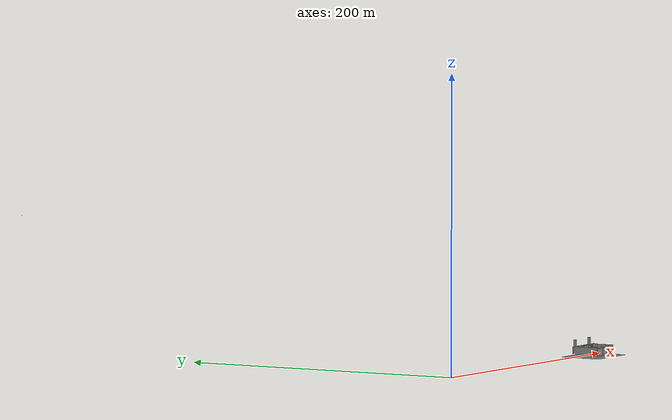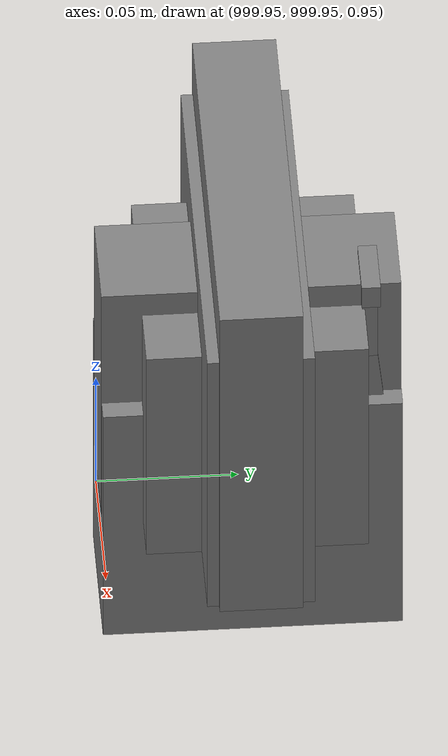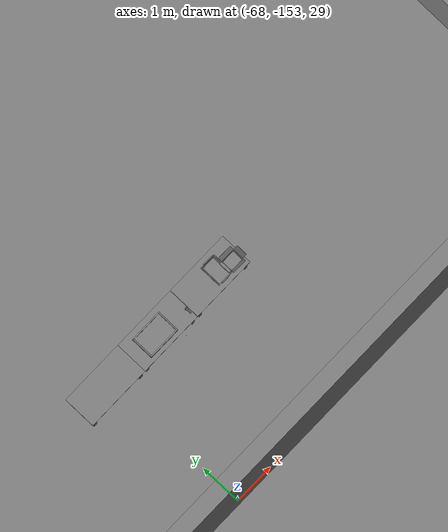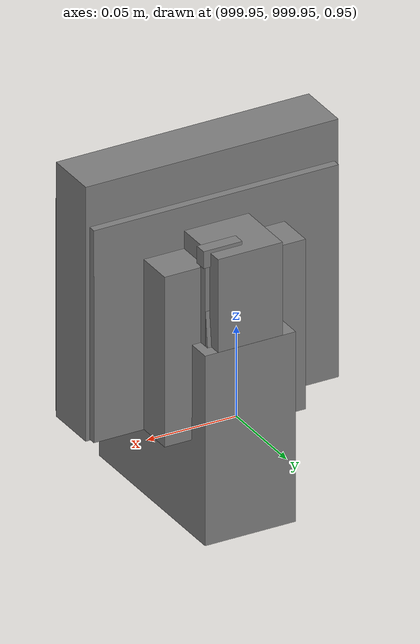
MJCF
<mujoco>
    <option gravity="0.000000000 0.000000000 -9.810000420" timestep="0.0049999999" integrator="implicitfast" density="1.225" viscosity="1.8000001e-05" noslip_iterations="10" iterations="100" sdf_iterations="50">
        <flag multiccd="disable"/>
    </option>
    <size memory="1000M"/>
    <compiler coordinate="local"/>
    <worldbody>
        <light cutoff="30" pos="0 1 1" dir="0 -1 -2"/>
        <light cutoff="30" pos="0 -1 1" dir="0 1 -2"/>
        <body pos="-64.866622925 -149.383972168 30.183746338" euler="89.999984741 89.999946594 0.000000000" name="openloong_gripper_2f85_fix_base_usda_bluebox_01">
            <geom contype="1" conaffinity="1" density="1000" type="box" material="" rgba="0.500000000 0.500000000 0.500000000 1.000000000" solimp="0.899999976 0.949999988 0.001000000" friction="1.000000000 0.005000000 0.000100000" solref="0.020000000 1.000000000" margin="0" condim="3" group="0" pos="0.276580811 0.187225342 0.000068665" quat="0.707106948 0.000077471 0.707106352 0.000077486" size="0.100000001 0.057999998 0.010000000" name="openloong_gripper_2f85_fix_base_usda_geom_5B902F18_EF4A_4D23_AAA4_A35915A8D042"/>
            <geom contype="1" conaffinity="1" density="1000" type="box" material="" rgba="0.500000000 0.500000000 0.500000000 1.000000000" solimp="0.899999976 0.949999988 0.001000000" friction="1.000000000 0.005000000 0.000100000" solref="0.020000000 1.000000000" margin="0" condim="3" group="0" pos="0.000000000 0.002883911 0.000000000" quat="0.999999881 0.000000000 0.000000000 0.000000000" size="0.254000008 0.003000000 0.172000006" name="openloong_gripper_2f85_fix_base_usda_geom_9C8130EF_13E1_404F_9641_6720F9C39A4A"/>
            <geom contype="1" conaffinity="1" density="1000" type="box" material="" rgba="0.500000000 0.500000000 0.500000000 1.000000000" solimp="0.899999976 0.949999988 0.001000000" friction="1.000000000 0.005000000 0.000100000" solref="0.020000000 1.000000000" margin="0" condim="3" group="0" pos="0.000000000 0.124874115 0.173484802" quat="0.999796331 0.020176515 -0.000000015 0.000000030" size="0.259999990 0.119999997 0.007000000" name="openloong_gripper_2f85_fix_base_usda_geom_24DBD5CA_9308_4937_83D9_7F573E8D2A75"/>
            <geom contype="1" conaffinity="1" density="1000" type="box" material="" rgba="0.500000000 0.500000000 0.500000000 1.000000000" solimp="0.899999976 0.949999988 0.001000000" friction="1.000000000 0.005000000 0.000100000" solref="0.020000000 1.000000000" margin="0" condim="3" group="0" pos="0.000000000 0.124874115 -0.173469543" quat="0.999796331 -0.020176545 -0.000000015 0.000000000" size="0.259999990 0.119999997 0.007000000" name="openloong_gripper_2f85_fix_base_usda_geom_C0D93C70_6401_4905_AC71_4A3B5EAA33F1"/>
            <geom contype="1" conaffinity="1" density="1000" type="box" material="" rgba="0.500000000 0.500000000 0.500000000 1.000000000" solimp="0.899999976 0.949999988 0.001000000" friction="1.000000000 0.005000000 0.000100000" solref="0.020000000 1.000000000" margin="0" condim="3" group="0" pos="0.000000000 0.214008331 0.188980103" quat="0.999912977 0.013176724 0.000000015 0.000000000" size="0.259999990 0.029999999 0.012500000" name="openloong_gripper_2f85_fix_base_usda_geom_E075266F_1476_416D_A384_15566D78F82A"/>
            <geom contype="1" conaffinity="1" density="1000" type="box" material="" rgba="0.500000000 0.500000000 0.500000000 1.000000000" solimp="0.899999976 0.949999988 0.001000000" friction="1.000000000 0.005000000 0.000100000" solref="0.020000000 1.000000000" margin="0" condim="3" group="0" pos="-0.258361816 0.125289917 0.001876831" quat="0.702796936 -0.020792112 0.710783124 0.020769298" size="0.189999998 0.119999997 0.009000000" name="openloong_gripper_2f85_fix_base_usda_geom_F2F7DE0F_1A2C_4287_93A0_17097038B397"/>
            <geom contype="1" conaffinity="1" density="1000" type="box" material="" rgba="0.500000000 0.500000000 0.500000000 1.000000000" solimp="0.899999976 0.949999988 0.001000000" friction="1.000000000 0.005000000 0.000100000" solref="0.020000000 1.000000000" margin="0" condim="3" group="0" pos="0.000000000 0.214008331 -0.188980103" quat="0.999912977 -0.013176769 0.000000030 0.000000015" size="0.259999990 0.029999999 0.012500000" name="openloong_gripper_2f85_fix_base_usda_geom_8FFEEB77_E183_4394_8FFB_05AC57A4C42B"/>
            <geom contype="1" conaffinity="1" density="1000" type="box" material="" rgba="0.500000000 0.500000000 0.500000000 1.000000000" solimp="0.899999976 0.949999988 0.001000000" friction="1.000000000 0.005000000 0.000100000" solref="0.020000000 1.000000000" margin="0" condim="3" group="0" pos="-0.276611328 0.187225342 0.000068665" quat="0.707106650 0.000077441 0.707106709 0.000077456" size="0.100000001 0.057999998 0.010000000" name="openloong_gripper_2f85_fix_base_usda_geom_FB21755A_31D8_4EC1_8092_953B2458F402"/>
            <geom contype="1" conaffinity="1" density="1000" type="box" material="" rgba="0.500000000 0.500000000 0.500000000 1.000000000" solimp="0.899999976 0.949999988 0.001000000" friction="1.000000000 0.005000000 0.000100000" solref="0.020000000 1.000000000" margin="0" condim="3" group="0" pos="0.258331299 0.125289917 0.001876831" quat="0.702851415 0.018856421 0.710823774 -0.019329369" size="0.189999998 0.119999997 0.009000000" name="openloong_gripper_2f85_fix_base_usda_geom_0B970599_CF49_4C41_8523_50C8F1CFB556"/>
            <freejoint name="openloong_gripper_2f85_fix_base_usda_bluebox_01_joint"/>
            <site size="0.005000000 0.005000000 0.005000000" rgba="0.500000000 0.500000000 0.500000000 1.000000000" pos="0.000000000 0.000000000 0.000000000" quat="0.999961913 0.008726534 0.000000000 0.000000000" group="0" type="sphere" name="openloong_gripper_2f85_fix_base_usda_bluebox_01site"/>
        </body>
        <body pos="-64.496299744 -149.491867065 30.235729218" euler="0.000000000 0.000000000 89.999946594" name="openloong_gripper_2f85_fix_base_usda_cardboardbox_01">
            <geom contype="1" conaffinity="1" density="1000" type="box" material="" rgba="0.500000000 0.500000000 0.500000000 1.000000000" solimp="0.899999976 0.949999988 0.001000000" friction="1.000000000 0.005000000 0.000100000" solref="0.020000000 1.000000000" margin="0" condim="3" group="0" pos="-0.003166199 -0.004086494 0.005052090" quat="1.000000000 0.000000000 0.000000000 0.000000000" size="0.142499998 0.177500010 0.005000000" name="openloong_gripper_2f85_fix_base_usda_geom_000B3867_FC23_42C7_A920_D5059A6079A3"/>
            <geom contype="1" conaffinity="1" density="1000" type="box" material="" rgba="0.500000000 0.500000000 0.500000000 1.000000000" solimp="0.899999976 0.949999988 0.001000000" friction="1.000000000 0.005000000 0.000100000" solref="0.020000000 1.000000000" margin="0" condim="3" group="0" pos="-0.003166199 0.170316696 0.150570869" quat="1.000000000 0.000000000 0.000000000 0.000000000" size="0.142499998 0.005000000 0.149999991" name="openloong_gripper_2f85_fix_base_usda_geom_8FB9CAC2_D835_40E7_B31B_57D6774E17F9"/>
            <geom contype="1" conaffinity="1" density="1000" type="box" material="" rgba="0.500000000 0.500000000 0.500000000 1.000000000" solimp="0.899999976 0.949999988 0.001000000" friction="1.000000000 0.005000000 0.000100000" solref="0.020000000 1.000000000" margin="0" condim="3" group="0" pos="-0.147399902 -0.005307198 0.150570869" quat="1.000000000 0.000000000 0.000000000 0.000000000" size="0.005000000 0.177500010 0.149999991" name="openloong_gripper_2f85_fix_base_usda_geom_3872AD21_D29D_463F_8400_300CF69918BF"/>
            <geom contype="1" conaffinity="1" density="1000" type="box" material="" rgba="0.500000000 0.500000000 0.500000000 1.000000000" solimp="0.899999976 0.949999988 0.001000000" friction="1.000000000 0.005000000 0.000100000" solref="0.020000000 1.000000000" margin="0" condim="3" group="0" pos="0.140275955 -0.005307198 0.150570869" quat="1.000000000 0.000000000 0.000000000 0.000000000" size="0.005000000 0.177500010 0.149999991" name="openloong_gripper_2f85_fix_base_usda_geom_20F7C4B4_BDB0_483B_8B92_E611F04E5AC0"/>
            <geom contype="1" conaffinity="1" density="1000" type="box" material="" rgba="0.500000000 0.500000000 0.500000000 1.000000000" solimp="0.899999976 0.949999988 0.001000000" friction="1.000000000 0.005000000 0.000100000" solref="0.020000000 1.000000000" margin="0" condim="3" group="0" pos="-0.003166199 -0.181550980 0.150570869" quat="1.000000000 0.000000000 0.000000000 0.000000000" size="0.142499998 0.005000000 0.149999991" name="openloong_gripper_2f85_fix_base_usda_geom_C0E9A1CF_670A_48CF_9FD0_678D82C4E1FA"/>
            <freejoint name="openloong_gripper_2f85_fix_base_usda_cardboardbox_01_joint"/>
            <site size="0.005000000 0.005000000 0.005000000" rgba="0.500000000 0.500000000 0.500000000 1.000000000" pos="0.000000000 0.000000000 0.000000000" quat="0.999961913 0.008726535 0.000000000 0.000000000" group="0" type="sphere" name="openloong_gripper_2f85_fix_base_usda_site_59161ED1_D4F0_4BA6_A373_8270CE4954D7"/>
            <body pos="0.139160156 -0.004048347 0.301930904" euler="-179.999954224 49.383502960 179.999954224" name="openloong_gripper_2f85_fix_base_usda_A1_006">
                <geom contype="1" conaffinity="1" density="1000" type="box" material="" rgba="0.500000000 0.500000000 0.500000000 1.000000000" solimp="0.899999976 0.949999988 0.001000000" friction="1.000000000 0.005000000 0.000100000" solref="0.020000000 1.000000000" margin="0" condim="3" group="0" pos="-0.071587563 0.000009537 0.001745224" quat="0.999999881 0.000000000 0.000000000 0.000000000" size="0.071249999 0.179999992 0.002500000" name="openloong_gripper_2f85_fix_base_usda_geom_5455E8E8_8F74_4F6F_B18F_721C24529E91"/>
                <joint armature="0" stiffness="0.07" damping="0.0099999998" axis="0.000000 1.000000 0.000000" type="hinge" name="openloong_gripper_2f85_fix_base_usda_A1_006"/>
            </body>
            <body pos="-0.145902634 -0.004086494 0.301938057" euler="-180.000000000 -60.000011444 -180.000000000" name="openloong_gripper_2f85_fix_base_usda_A2_006">
                <geom contype="1" conaffinity="1" density="1000" type="box" material="" rgba="0.500000000 0.500000000 0.500000000 1.000000000" solimp="0.899999976 0.949999988 0.001000000" friction="1.000000000 0.005000000 0.000100000" solref="0.020000000 1.000000000" margin="0" condim="3" group="0" pos="0.071268082 0.000009537 0.002717972" quat="0.000002921 0.000000000 -0.000000030 0.999999881" size="0.071249999 0.179999992 0.002500000" name="openloong_gripper_2f85_fix_base_usda_geom_B7B3E422_3CE8_41DB_99AA_EF75294D3759"/>
                <joint armature="0" stiffness="0.07" damping="0.0099999998" axis="0.000000 1.000000 0.000000" type="hinge" name="openloong_gripper_2f85_fix_base_usda_A2_006"/>
            </body>
            <body pos="-0.003385544 0.175991058 0.301930904" euler="-125.858116150 -0.000004561 0.000002331" name="openloong_gripper_2f85_fix_base_usda_B2_006">
                <geom contype="1" conaffinity="1" density="1000" type="box" material="" rgba="0.500000000 0.500000000 0.500000000 1.000000000" solimp="0.899999976 0.949999988 0.001000000" friction="1.000000000 0.005000000 0.000100000" solref="0.020000000 1.000000000" margin="0" condim="3" group="0" pos="0.000009537 -0.070939064 -0.002470016" quat="0.999614120 0.027776197 -0.000000015 0.000000030" size="0.137500003 0.064999998 0.005000000" name="openloong_gripper_2f85_fix_base_usda_geom_E5C7E1CF_653D_4D78_8F2D_44F1880D7AD4"/>
                <joint armature="0" stiffness="0.07" damping="0.0099999998" axis="1.000000 0.000000 0.000000" type="hinge" name="openloong_gripper_2f85_fix_base_usda_B2_006"/>
            </body>
            <body pos="-0.003385544 -0.184140205 0.301938057" euler="147.805557251 0.000000000 0.000000000" name="openloong_gripper_2f85_fix_base_usda_B1_006">
                <geom contype="1" conaffinity="1" density="1000" type="box" material="" rgba="0.500000000 0.500000000 0.500000000 1.000000000" solimp="0.899999976 0.949999988 0.001000000" friction="1.000000000 0.005000000 0.000100000" solref="0.020000000 1.000000000" margin="0" condim="3" group="0" pos="-0.000028610 0.070202351 -0.002703667" quat="0.999614179 -0.027776167 0.000000000 0.000000000" size="0.137500003 0.064999998 0.005000000" name="openloong_gripper_2f85_fix_base_usda_geom_EF0CE5E7_4E79_4D61_864D_DDC74DC2FF79"/>
                <joint armature="0" stiffness="0.07" damping="0.0099999998" axis="1.000000 0.000000 0.000000" type="hinge" name="openloong_gripper_2f85_fix_base_usda_B1_006"/>
            </body>
        </body>
        <body pos="-65.882858276 -149.481979370 30.229999542" euler="-64.487716675 0.000000000 0.000000000" name="openloong_gripper_2f85_fix_base_usda_Barcode">
            <geom contype="1" conaffinity="1" density="1000" type="box" material="" rgba="0.500000000 0.500000000 0.500000000 1.000000000" solimp="0.899999976 0.949999988 0.001000000" friction="1.000000000 0.005000000 0.000100000" solref="0.020000000 1.000000000" margin="0" condim="3" group="0" pos="0.000000000 0.013038635 0.001419067" quat="0.000000000 0.000000000 0.000000000 1.000000119" size="0.034000002 0.010000000 0.017999999" name="openloong_gripper_2f85_fix_base_usda_geom_23EDB624_BAD7_4948_AEA4_5A858636DA06"/>
            <geom contype="1" conaffinity="1" density="1000" type="box" material="" rgba="0.500000000 0.500000000 0.500000000 1.000000000" solimp="0.899999976 0.949999988 0.001000000" friction="1.000000000 0.005000000 0.000100000" solref="0.020000000 1.000000000" margin="0" condim="3" group="0" pos="0.000000000 -0.035301208 -0.007095337" quat="0.000000000 0.000000000 -0.043619365 0.999048233" size="0.028999999 0.010000000 0.020000000" name="openloong_gripper_2f85_fix_base_usda_geom_1C69C142_55A9_42A4_876C_107EED3B5D65"/>
            <geom contype="1" conaffinity="1" density="1000" type="box" material="" rgba="0.500000000 0.500000000 0.500000000 1.000000000" solimp="0.899999976 0.949999988 0.001000000" friction="1.000000000 0.005000000 0.000100000" solref="0.020000000 1.000000000" margin="0" condim="3" group="0" pos="0.000000000 -0.043411255 -0.011749268" quat="0.922262907 0.386563420 0.000000000 0.000000000" size="0.026000001 0.010000000 0.020000000" name="openloong_gripper_2f85_fix_base_usda_geom_A1ABBBA7_F5E7_4971_89C0_9C8ABEADA9D7"/>
            <geom contype="1" conaffinity="1" density="1000" type="box" material="" rgba="0.500000000 0.500000000 0.500000000 1.000000000" solimp="0.899999976 0.949999988 0.001000000" friction="1.000000000 0.005000000 0.000100000" solref="0.020000000 1.000000000" margin="0" condim="3" group="0" pos="0.000000000 -0.016967773 -0.031860352" quat="0.000000000 0.000000000 0.000000000 1.000000119" size="0.008000000 0.010000000 0.013000000" name="openloong_gripper_2f85_fix_base_usda_geom_49ACC6EB_F449_4084_BF7B_38D5CFA1FBE2"/>
            <geom contype="1" conaffinity="1" density="1000" type="box" material="" rgba="0.500000000 0.500000000 0.500000000 1.000000000" solimp="0.899999976 0.949999988 0.001000000" friction="1.000000000 0.005000000 0.000100000" solref="0.020000000 1.000000000" margin="0" condim="3" group="0" pos="0.000000000 -0.001869202 0.000312805" quat="0.953716993 0.300705761 0.000000000 0.000000000" size="0.032000002 0.010000000 0.018999999" name="openloong_gripper_2f85_fix_base_usda_geom_5DC06A53_019B_4E08_A66A_0D58FE93D02F"/>
            <geom contype="1" conaffinity="1" density="1000" type="box" material="" rgba="0.500000000 0.500000000 0.500000000 1.000000000" solimp="0.899999976 0.949999988 0.001000000" friction="1.000000000 0.005000000 0.000100000" solref="0.020000000 1.000000000" margin="0" condim="3" group="0" pos="0.000000000 -0.019531250 -0.003173828" quat="0.953716993 0.300705761 0.000000000 0.000000000" size="0.030999999 0.010000000 0.020000000" name="openloong_gripper_2f85_fix_base_usda_geom_CAE066BE_592E_42AE_870B_6F61BBCDE782"/>
            <geom contype="1" conaffinity="1" density="1000" type="box" material="" rgba="0.500000000 0.500000000 0.500000000 1.000000000" solimp="0.899999976 0.949999988 0.001000000" friction="1.000000000 0.005000000 0.000100000" solref="0.020000000 1.000000000" margin="0" condim="3" group="0" pos="0.000000000 -0.035301208 -0.007095337" quat="0.953716993 0.300705761 0.000000000 0.000000000" size="0.028999999 0.010000000 0.020000000" name="openloong_gripper_2f85_fix_base_usda_geom_EB980E29_2712_433A_A395_D4AABACDE76B"/>
            <geom contype="1" conaffinity="1" density="1000" type="box" material="" rgba="0.500000000 0.500000000 0.500000000 1.000000000" solimp="0.899999976 0.949999988 0.001000000" friction="1.000000000 0.005000000 0.000100000" solref="0.020000000 1.000000000" margin="0" condim="3" group="0" pos="0.000000000 -0.042617798 -0.071121216" quat="0.000000000 0.000000000 0.000000000 1.000000119" size="0.013000000 0.021000000 0.059999999" name="openloong_gripper_2f85_fix_base_usda_geom_E717F6F5_7B2B_4F51_8991_96CB8587E2FF"/>
            <freejoint name="openloong_gripper_2f85_fix_base_usda_Barcode_joint"/>
            <site size="0.005000000 0.005000000 0.005000000" rgba="0.500000000 0.500000000 0.500000000 1.000000000" pos="0.000000000 0.000000000 0.000000000" quat="1.000000000 0.000000000 0.000000000 0.000000000" group="0" type="sphere" name="openloong_gripper_2f85_fix_base_usda_Barcode_site"/>
        </body>
        <body pos="-66.745018005 -149.392349243 30.184000015" euler="0.000000000 0.000000000 89.999946594" name="[22329932595678]_Basket_01">
            <geom contype="1" conaffinity="1" density="1000" type="box" material="" rgba="0.500000000 0.500000000 0.500000000 1.000000000" solimp="0.899999976 0.949999988 0.001000000" friction="1.000000000 0.005000000 0.000100000" solref="0.020000000 1.000000000" margin="0" condim="3" group="0" pos="-0.052425385 0.389207840 0.089787483" quat="0.707107008 0.000000000 0.000000000 0.707106411" size="0.014249999 0.014249999 0.059999999" name="[22329932595678]_geom_E796105B_9C38_4C3E_86CA_14755D51C3E3"/>
            <geom contype="1" conaffinity="1" density="1000" type="box" material="" rgba="0.500000000 0.500000000 0.500000000 1.000000000" solimp="0.899999976 0.949999988 0.001000000" friction="1.000000000 0.005000000 0.000100000" solref="0.020000000 1.000000000" margin="0" condim="3" group="0" pos="0.264015198 -0.133043289 0.089787483" quat="0.707107008 0.000000000 0.000000000 0.707106411" size="0.014249999 0.014249999 0.059999999" name="[22329932595678]_geom_D94942E2_CEBB_4C4A_93C0_6F68312A178F"/>
            <geom contype="1" conaffinity="1" density="1000" type="box" material="" rgba="0.500000000 0.500000000 0.500000000 1.000000000" solimp="0.899999976 0.949999988 0.001000000" friction="1.000000000 0.005000000 0.000100000" solref="0.020000000 1.000000000" margin="0" condim="3" group="0" pos="-0.264015198 -0.265548706 0.089793205" quat="0.707107008 0.000000000 0.000000000 0.707106411" size="0.014249999 0.014249999 0.059999999" name="[22329932595678]_geom_E79E49B3_2E30_4AE6_BDEF_54CAAE42C273"/>
            <geom contype="1" conaffinity="1" density="1000" type="box" material="" rgba="0.500000000 0.500000000 0.500000000 1.000000000" solimp="0.899999976 0.949999988 0.001000000" friction="1.000000000 0.005000000 0.000100000" solref="0.020000000 1.000000000" margin="0" condim="3" group="0" pos="-0.160263062 -0.389322281 0.089793205" quat="0.707107008 0.000000000 0.000000000 0.707106411" size="0.014249999 0.014249999 0.059999999" name="[22329932595678]_geom_212C27CF_6D50_4FB7_B477_7AA481C25F40"/>
            <geom contype="1" conaffinity="1" density="1000" type="box" material="" rgba="0.500000000 0.500000000 0.500000000 1.000000000" solimp="0.899999976 0.949999988 0.001000000" friction="1.000000000 0.005000000 0.000100000" solref="0.020000000 1.000000000" margin="0" condim="3" group="0" pos="0.162265778 -0.389322281 0.089787483" quat="0.707107008 0.000000000 0.000000000 0.707106411" size="0.014249999 0.014249999 0.059999999" name="[22329932595678]_geom_A4F51743_E59F_48E7_8637_1E60DCAB5018"/>
            <geom contype="1" conaffinity="1" density="1000" type="box" material="" rgba="0.500000000 0.500000000 0.500000000 1.000000000" solimp="0.899999976 0.949999988 0.001000000" friction="1.000000000 0.005000000 0.000100000" solref="0.020000000 1.000000000" margin="0" condim="3" group="0" pos="0.264015198 0.389207840 0.089787483" quat="0.707107008 0.000000000 0.000000000 0.707106411" size="0.014249999 0.014249999 0.059999999" name="[22329932595678]_geom_D5D64BFA_32FD_47BE_A040_ED928FA09D8F"/>
            <geom contype="1" conaffinity="1" density="1000" type="box" material="" rgba="0.500000000 0.500000000 0.500000000 1.000000000" solimp="0.899999976 0.949999988 0.001000000" friction="1.000000000 0.005000000 0.000100000" solref="0.020000000 1.000000000" margin="0" condim="3" group="0" pos="-0.264015198 -0.133043289 0.089793205" quat="0.707107008 0.000000000 0.000000000 0.707106411" size="0.014249999 0.014249999 0.059999999" name="[22329932595678]_geom_E9E26756_2410_4FEC_B6BB_96962F9296EF"/>
            <geom contype="1" conaffinity="1" density="1000" type="box" material="" rgba="0.500000000 0.500000000 0.500000000 1.000000000" solimp="0.899999976 0.949999988 0.001000000" friction="1.000000000 0.005000000 0.000100000" solref="0.020000000 1.000000000" margin="0" condim="3" group="0" pos="-0.264026642 0.269256592 0.089793205" quat="0.707107008 0.000000000 0.000000000 0.707106411" size="0.014249999 0.014249999 0.059999999" name="[22329932595678]_geom_D35B0350_C500_4B1E_8BD5_7B5485365403"/>
            <geom contype="1" conaffinity="1" density="1000" type="box" material="" rgba="0.500000000 0.500000000 0.500000000 1.000000000" solimp="0.899999976 0.949999988 0.001000000" friction="1.000000000 0.005000000 0.000100000" solref="0.020000000 1.000000000" margin="0" condim="3" group="0" pos="0.054462433 0.389207840 0.089787483" quat="0.707107008 0.000000000 0.000000000 0.707106411" size="0.014249999 0.014249999 0.059999999" name="[22329932595678]_geom_A9B55AF4_7E98_45F5_919D_C04AC8B14143"/>
            <geom contype="1" conaffinity="1" density="1000" type="box" material="" rgba="0.500000000 0.500000000 0.500000000 1.000000000" solimp="0.899999976 0.949999988 0.001000000" friction="1.000000000 0.005000000 0.000100000" solref="0.020000000 1.000000000" margin="0" condim="3" group="0" pos="0.054462433 -0.389322281 0.089787483" quat="0.707107008 0.000000000 0.000000000 0.707106411" size="0.014249999 0.014249999 0.059999999" name="[22329932595678]_geom_F4D8A637_9881_4A1F_857C_0B8FC4DBA830"/>
            <geom contype="1" conaffinity="1" density="1000" type="box" material="" rgba="0.500000000 0.500000000 0.500000000 1.000000000" solimp="0.899999976 0.949999988 0.001000000" friction="1.000000000 0.005000000 0.000100000" solref="0.020000000 1.000000000" margin="0" condim="3" group="0" pos="0.264015198 0.269256592 0.089793205" quat="0.707107008 0.000000000 0.000000000 0.707106411" size="0.014249999 0.014249999 0.059999999" name="[22329932595678]_geom_3FA5FEE9_CB6C_4D05_8DE2_9F4061AD9249"/>
            <geom contype="1" conaffinity="1" density="1000" type="box" material="" rgba="0.500000000 0.500000000 0.500000000 1.000000000" solimp="0.899999976 0.949999988 0.001000000" friction="1.000000000 0.005000000 0.000100000" solref="0.020000000 1.000000000" margin="0" condim="3" group="0" pos="0.264015198 -0.389322281 0.089787483" quat="0.707107008 0.000000000 0.000000000 0.707106411" size="0.014249999 0.014249999 0.059999999" name="[22329932595678]_geom_C8023261_D4C8_4ABC_8FE3_B767FDDE7A12"/>
            <geom contype="1" conaffinity="1" density="1000" type="box" material="" rgba="0.500000000 0.500000000 0.500000000 1.000000000" solimp="0.899999976 0.949999988 0.001000000" friction="1.000000000 0.005000000 0.000100000" solref="0.020000000 1.000000000" margin="0" condim="3" group="0" pos="0.000000000 0.000000000 0.015998840" quat="0.707107008 0.000000000 0.000000000 0.707106411" size="0.403499991 0.279000014 0.015750000" name="[22329932595678]_geom_BFB86EE3_96F3_4917_BDB4_0643A8A1C79E"/>
            <geom contype="1" conaffinity="1" density="1000" type="box" material="" rgba="0.500000000 0.500000000 0.500000000 1.000000000" solimp="0.899999976 0.949999988 0.001000000" friction="1.000000000 0.005000000 0.000100000" solref="0.020000000 1.000000000" margin="0" condim="3" group="0" pos="0.000000000 -0.389476776 0.163619041" quat="0.707107008 0.000000000 0.000000000 0.707106411" size="0.015000000 0.277500004 0.015750000" name="[22329932595678]_geom_B5E44797_99DC_44F5_B118_E231478292D4"/>
            <geom contype="1" conaffinity="1" density="1000" type="box" material="" rgba="0.500000000 0.500000000 0.500000000 1.000000000" solimp="0.899999976 0.949999988 0.001000000" friction="1.000000000 0.005000000 0.000100000" solref="0.020000000 1.000000000" margin="0" condim="3" group="0" pos="0.162265778 0.389207840 0.089787483" quat="0.707107008 0.000000000 0.000000000 0.707106411" size="0.014249999 0.014249999 0.059999999" name="[22329932595678]_geom_C63AF8D9_BCFF_4D2C_8E4D_8766A5670B57"/>
            <geom contype="1" conaffinity="1" density="1000" type="box" material="" rgba="0.500000000 0.500000000 0.500000000 1.000000000" solimp="0.899999976 0.949999988 0.001000000" friction="1.000000000 0.005000000 0.000100000" solref="0.020000000 1.000000000" margin="0" condim="3" group="0" pos="0.000000000 0.389471054 0.163619041" quat="0.707107008 0.000000000 0.000000000 0.707106411" size="0.015000000 0.277500004 0.015750000" name="[22329932595678]_geom_BEAE133D_4BA4_4FD3_8B60_88E0B1940BF1"/>
            <geom contype="1" conaffinity="1" density="1000" type="box" material="" rgba="0.500000000 0.500000000 0.500000000 1.000000000" solimp="0.899999976 0.949999988 0.001000000" friction="1.000000000 0.005000000 0.000100000" solref="0.020000000 1.000000000" margin="0" condim="3" group="0" pos="-0.263511658 0.000000000 0.163619041" quat="0.707107008 0.000000000 0.000000000 0.707106411" size="0.403499991 0.015000000 0.015750000" name="[22329932595678]_geom_D24D300F_E6E0_4A58_9496_3F6E8C50C2AB"/>
            <geom contype="1" conaffinity="1" density="1000" type="box" material="" rgba="0.500000000 0.500000000 0.500000000 1.000000000" solimp="0.899999976 0.949999988 0.001000000" friction="1.000000000 0.005000000 0.000100000" solref="0.020000000 1.000000000" margin="0" condim="3" group="0" pos="-0.264015198 0.141334534 0.089793205" quat="0.707107008 0.000000000 0.000000000 0.707106411" size="0.014249999 0.014249999 0.059999999" name="[22329932595678]_geom_5A6CB990_D672_496C_8547_29537AC49627"/>
            <geom contype="1" conaffinity="1" density="1000" type="box" material="" rgba="0.500000000 0.500000000 0.500000000 1.000000000" solimp="0.899999976 0.949999988 0.001000000" friction="1.000000000 0.005000000 0.000100000" solref="0.020000000 1.000000000" margin="0" condim="3" group="0" pos="0.264015198 -0.265548706 0.089787483" quat="0.707107008 0.000000000 0.000000000 0.707106411" size="0.014249999 0.014249999 0.059999999" name="[22329932595678]_geom_95AC8412_E91B_4804_88FC_80D288B933A1"/>
            <geom contype="1" conaffinity="1" density="1000" type="box" material="" rgba="0.500000000 0.500000000 0.500000000 1.000000000" solimp="0.899999976 0.949999988 0.001000000" friction="1.000000000 0.005000000 0.000100000" solref="0.020000000 1.000000000" margin="0" condim="3" group="0" pos="-0.160263062 0.389207840 0.089787483" quat="0.707107008 0.000000000 0.000000000 0.707106411" size="0.014249999 0.014249999 0.059999999" name="[22329932595678]_geom_65ACCF73_4BA2_4A1F_A746_603EEC5F18EB"/>
            <geom contype="1" conaffinity="1" density="1000" type="box" material="" rgba="0.500000000 0.500000000 0.500000000 1.000000000" solimp="0.899999976 0.949999988 0.001000000" friction="1.000000000 0.005000000 0.000100000" solref="0.020000000 1.000000000" margin="0" condim="3" group="0" pos="-0.052425385 -0.389322281 0.089787483" quat="0.707107008 0.000000000 0.000000000 0.707106411" size="0.014249999 0.014249999 0.059999999" name="[22329932595678]_geom_0F9234E4_729F_4008_849D_1A87EE64E35B"/>
            <geom contype="1" conaffinity="1" density="1000" type="box" material="" rgba="0.500000000 0.500000000 0.500000000 1.000000000" solimp="0.899999976 0.949999988 0.001000000" friction="1.000000000 0.005000000 0.000100000" solref="0.020000000 1.000000000" margin="0" condim="3" group="0" pos="-0.264026642 -0.389322281 0.089793205" quat="0.707107008 0.000000000 0.000000000 0.707106411" size="0.014249999 0.014249999 0.059999999" name="[22329932595678]_geom_484C8111_CA97_415F_94E9_0F6AE297EB55"/>
            <geom contype="1" conaffinity="1" density="1000" type="box" material="" rgba="0.500000000 0.500000000 0.500000000 1.000000000" solimp="0.899999976 0.949999988 0.001000000" friction="1.000000000 0.005000000 0.000100000" solref="0.020000000 1.000000000" margin="0" condim="3" group="0" pos="0.264015198 0.141334534 0.089787483" quat="0.707107008 0.000000000 0.000000000 0.707106411" size="0.014249999 0.014249999 0.059999999" name="[22329932595678]_geom_87CC5386_9759_46E5_8584_D00FFF5069D0"/>
            <geom contype="1" conaffinity="1" density="1000" type="box" material="" rgba="0.500000000 0.500000000 0.500000000 1.000000000" solimp="0.899999976 0.949999988 0.001000000" friction="1.000000000 0.005000000 0.000100000" solref="0.020000000 1.000000000" margin="0" condim="3" group="0" pos="-0.264015198 0.389207840 0.089793205" quat="0.707107008 0.000000000 0.000000000 0.707106411" size="0.014249999 0.014249999 0.059999999" name="[22329932595678]_geom_AC3262E1_F5BD_44F0_8B42_6C9BDD18FFAC"/>
            <geom contype="1" conaffinity="1" density="1000" type="box" material="" rgba="0.500000000 0.500000000 0.500000000 1.000000000" solimp="0.899999976 0.949999988 0.001000000" friction="1.000000000 0.005000000 0.000100000" solref="0.020000000 1.000000000" margin="0" condim="3" group="0" pos="0.264015198 0.004480362 0.089787483" quat="0.707107008 0.000000000 0.000000000 0.707106411" size="0.014249999 0.014249999 0.059999999" name="[22329932595678]_geom_3C732A37_0EA0_45CE_B359_7CFBF70F1592"/>
            <geom contype="1" conaffinity="1" density="1000" type="box" material="" rgba="0.500000000 0.500000000 0.500000000 1.000000000" solimp="0.899999976 0.949999988 0.001000000" friction="1.000000000 0.005000000 0.000100000" solref="0.020000000 1.000000000" margin="0" condim="3" group="0" pos="0.263694763 -0.000011444 0.163619041" quat="0.707107008 0.000000000 0.000000000 0.707106411" size="0.403499991 0.015000000 0.015750000" name="[22329932595678]_geom_1607EE69_2971_4C17_84FE_ED1BADCF3623"/>
            <geom contype="1" conaffinity="1" density="1000" type="box" material="" rgba="0.500000000 0.500000000 0.500000000 1.000000000" solimp="0.899999976 0.949999988 0.001000000" friction="1.000000000 0.005000000 0.000100000" solref="0.020000000 1.000000000" margin="0" condim="3" group="0" pos="-0.264015198 0.004480362 0.089793205" quat="0.707107008 0.000000000 0.000000000 0.707106411" size="0.014249999 0.014249999 0.059999999" name="[22329932595678]_geom_D06F78C7_A8A3_4B6F_9455_739BD94867E1"/>
            <freejoint name="[22329932595678]_joint_CE649FBB_59A3_4CE6_9021_04710817D87C"/>
        </body>
        <body pos="0.000000000 0.000000000 0.000000000" euler="0.000000000 0.000000000 0.000000000" name="Static Objects_Static Objects">
            <geom contype="1" conaffinity="1" density="1000" type="box" material="" rgba="0.500000000 0.500000000 0.500000000 1.000000000" solimp="0.899999976 0.949999988 0.001000000" friction="1.000000000 0.005000000 0.000100000" solref="0.020000000 1.000000000" margin="0" condim="3" group="0" pos="-67.544113159 -149.365814209 29.727830887" quat="0.500000417 0.499999970 0.499999553 0.499999970" size="0.381000012 0.319999993 0.041000001" name="Static Objects_geom_CF97E724_04D7_4C04_9F95_9A88C545F1C4"/>
            <geom contype="1" conaffinity="1" density="1000" type="box" material="" rgba="0.500000000 0.500000000 0.500000000 1.000000000" solimp="0.899999976 0.949999988 0.001000000" friction="1.000000000 0.005000000 0.000100000" solref="0.020000000 1.000000000" margin="0" condim="3" group="0" pos="-68.239501953 -149.365814209 30.086868286" quat="0.500000417 0.499999970 0.499999553 0.499999970" size="0.370999992 0.039500002 0.745000005" name="Static Objects_geom_A69FE707_0A1D_445A_82AF_1DFABADAC3FC"/>
            <geom contype="1" conaffinity="1" density="1000" type="box" material="" rgba="0.500000000 0.500000000 0.500000000 1.000000000" solimp="0.899999976 0.949999988 0.001000000" friction="1.000000000 0.005000000 0.000100000" solref="0.020000000 1.000000000" margin="0" condim="3" group="0" pos="-68.239501953 -149.365814209 30.147235870" quat="0.500000417 0.499999970 0.499999553 0.499999970" size="0.400000006 0.022000000 0.800000012" name="Static Objects_geom_C5A78421_9171_401F_B896_E58A61681704"/>
            <geom contype="1" conaffinity="1" density="1000" type="box" material="" rgba="0.500000000 0.500000000 0.500000000 1.000000000" solimp="0.899999976 0.949999988 0.001000000" friction="1.000000000 0.005000000 0.000100000" solref="0.020000000 1.000000000" margin="0" condim="3" group="0" pos="-68.934890747 -149.365814209 29.727830887" quat="0.500000417 0.499999970 0.499999553 0.499999970" size="0.381000012 0.319999993 0.041000001" name="Static Objects_geom_1A28B2D4_42F8_4725_8683_877264033F15"/>
            <geom contype="1" conaffinity="1" density="1000" type="box" material="" rgba="0.500000000 0.500000000 0.500000000 1.000000000" solimp="0.899999976 0.949999988 0.001000000" friction="1.000000000 0.005000000 0.000100000" solref="0.020000000 1.000000000" margin="0" condim="3" group="0" pos="-68.239501953 -149.365814209 29.561563492" quat="0.500000417 0.499999970 0.499999553 0.499999970" size="0.020000000 0.022000000 0.660000026" name="Static Objects_geom_10D87C88_4FE4_4D3F_8429_5A416A274568"/>
            <geom contype="1" conaffinity="1" density="1000" type="box" material="" rgba="0.500000000 0.500000000 0.500000000 1.000000000" solimp="0.899999976 0.949999988 0.001000000" friction="1.000000000 0.005000000 0.000100000" solref="0.020000000 1.000000000" margin="0" condim="3" group="0" pos="-65.945671082 -149.365814209 29.727830887" quat="0.500000417 0.499999970 0.499999553 0.499999970" size="0.381000012 0.319999993 0.041000001" name="Static Objects_geom_FC7C8C3A_AD3A_4688_9D73_6AE27E6C833C"/>
            <geom contype="1" conaffinity="1" density="1000" type="box" material="" rgba="0.500000000 0.500000000 0.500000000 1.000000000" solimp="0.899999976 0.949999988 0.001000000" friction="1.000000000 0.005000000 0.000100000" solref="0.020000000 1.000000000" margin="0" condim="3" group="0" pos="-66.641059875 -149.365814209 30.086868286" quat="0.500000417 0.499999970 0.499999553 0.499999970" size="0.370999992 0.039500002 0.745000005" name="Static Objects_geom_D8F8302B_CAA2_4BE4_ABB4_5F212A571588"/>
            <geom contype="1" conaffinity="1" density="1000" type="box" material="" rgba="0.500000000 0.500000000 0.500000000 1.000000000" solimp="0.899999976 0.949999988 0.001000000" friction="1.000000000 0.005000000 0.000100000" solref="0.020000000 1.000000000" margin="0" condim="3" group="0" pos="-66.641059875 -149.365814209 30.147235870" quat="0.500000417 0.499999970 0.499999553 0.499999970" size="0.400000006 0.022000000 0.800000012" name="Static Objects_geom_B907728B_5EDF_47B9_8345_109161BA570F"/>
            <geom contype="1" conaffinity="1" density="1000" type="box" material="" rgba="0.500000000 0.500000000 0.500000000 1.000000000" solimp="0.899999976 0.949999988 0.001000000" friction="1.000000000 0.005000000 0.000100000" solref="0.020000000 1.000000000" margin="0" condim="3" group="0" pos="-67.336448669 -149.365814209 29.727830887" quat="0.500000417 0.499999970 0.499999553 0.499999970" size="0.381000012 0.319999993 0.041000001" name="Static Objects_geom_3F56F35C_8449_4EA2_B9E2_3363CBD34075"/>
            <geom contype="1" conaffinity="1" density="1000" type="box" material="" rgba="0.500000000 0.500000000 0.500000000 1.000000000" solimp="0.899999976 0.949999988 0.001000000" friction="1.000000000 0.005000000 0.000100000" solref="0.020000000 1.000000000" margin="0" condim="3" group="0" pos="-66.641059875 -149.365814209 29.561563492" quat="0.500000417 0.499999970 0.499999553 0.499999970" size="0.020000000 0.022000000 0.660000026" name="Static Objects_geom_D8C1EDD0_8008_41F6_8E9D_E7354EBC8FF6"/>
            <geom contype="1" conaffinity="1" density="1000" type="box" material="" rgba="0.500000000 0.500000000 0.500000000 1.000000000" solimp="0.899999976 0.949999988 0.001000000" friction="1.000000000 0.005000000 0.000100000" solref="0.020000000 1.000000000" margin="0" condim="3" group="0" pos="-64.338577271 -149.365814209 29.727830887" quat="0.500000417 0.499999970 0.499999553 0.499999970" size="0.381000012 0.319999993 0.041000001" name="Static Objects_geom_09BDE61C_A954_4D91_9EBF_4426D1E65E6C"/>
            <geom contype="1" conaffinity="1" density="1000" type="box" material="" rgba="0.500000000 0.500000000 0.500000000 1.000000000" solimp="0.899999976 0.949999988 0.001000000" friction="1.000000000 0.005000000 0.000100000" solref="0.020000000 1.000000000" margin="0" condim="3" group="0" pos="-65.033966064 -149.365814209 30.086868286" quat="0.500000417 0.499999970 0.499999553 0.499999970" size="0.370999992 0.039500002 0.745000005" name="Static Objects_geom_08103C8E_2043_4198_AC39_531CA1C659BA"/>
            <geom contype="1" conaffinity="1" density="1000" type="box" material="" rgba="0.500000000 0.500000000 0.500000000 1.000000000" solimp="0.899999976 0.949999988 0.001000000" friction="1.000000000 0.005000000 0.000100000" solref="0.020000000 1.000000000" margin="0" condim="3" group="0" pos="-65.033966064 -149.365814209 30.147235870" quat="0.500000417 0.499999970 0.499999553 0.499999970" size="0.400000006 0.022000000 0.800000012" name="Static Objects_geom_B911341A_AFAB_40F5_9308_EA73453A8053"/>
            <geom contype="1" conaffinity="1" density="1000" type="box" material="" rgba="0.500000000 0.500000000 0.500000000 1.000000000" solimp="0.899999976 0.949999988 0.001000000" friction="1.000000000 0.005000000 0.000100000" solref="0.020000000 1.000000000" margin="0" condim="3" group="0" pos="-65.729354858 -149.365814209 29.727830887" quat="0.500000417 0.499999970 0.499999553 0.499999970" size="0.381000012 0.319999993 0.041000001" name="Static Objects_geom_388B6199_A3C5_457E_97C7_45C7736785E9"/>
            <geom contype="1" conaffinity="1" density="1000" type="box" material="" rgba="0.500000000 0.500000000 0.500000000 1.000000000" solimp="0.899999976 0.949999988 0.001000000" friction="1.000000000 0.005000000 0.000100000" solref="0.020000000 1.000000000" margin="0" condim="3" group="0" pos="-65.033966064 -149.365814209 29.561563492" quat="0.500000417 0.499999970 0.499999553 0.499999970" size="0.020000000 0.022000000 0.660000026" name="Static Objects_geom_710D263D_4083_4F25_ACB7_338F673A46E3"/>
            <geom contype="1" conaffinity="1" density="1000" type="box" material="" rgba="0.500000000 0.500000000 0.500000000 1.000000000" solimp="0.899999976 0.949999988 0.001000000" friction="1.000000000 0.005000000 0.000100000" solref="0.020000000 1.000000000" margin="0" condim="3" group="0" pos="-61.754566193 -137.853729248 33.906845093" quat="0.707107067 0.000000000 0.000000000 0.707106471" size="0.759999990 0.759999990 4.500000000" name="Static Objects_geom_962A1B7D_DB9E_4233_A28B_CCC84515840F"/>
            <geom contype="1" conaffinity="1" density="1000" type="box" material="" rgba="0.500000000 0.500000000 0.500000000 1.000000000" solimp="0.899999976 0.949999988 0.001000000" friction="1.000000000 0.005000000 0.000100000" solref="0.020000000 1.000000000" margin="0" condim="3" group="0" pos="-57.511135101 -144.927108765 31.707921982" quat="1.000000000 0.000000000 0.000000000 0.000000000" size="0.200000003 8.000000000 2.299999952" name="Static Objects_geom_5F2FE542_18E5_4BCB_B935_8FE68005384D"/>
            <geom contype="1" conaffinity="1" density="1000" type="box" material="" rgba="0.500000000 0.500000000 0.500000000 1.000000000" solimp="0.899999976 0.949999988 0.001000000" friction="1.000000000 0.005000000 0.000100000" solref="0.020000000 1.000000000" margin="0" condim="3" group="0" pos="-80.517646790 -157.574050903 31.688196182" quat="0.707107067 0.000000000 0.000000000 0.707106471" size="0.600000024 0.600000024 2.299999952" name="Static Objects_geom_E3FA90D5_7E41_4ED6_838D_0C392F80C510"/>
            <geom contype="1" conaffinity="1" density="1000" type="box" material="" rgba="0.500000000 0.500000000 0.500000000 1.000000000" solimp="0.899999976 0.949999988 0.001000000" friction="1.000000000 0.005000000 0.000100000" solref="0.020000000 1.000000000" margin="0" condim="3" group="0" pos="-80.711044312 -147.414932251 31.666158676" quat="1.000000000 0.000000000 0.000000000 0.000000000" size="0.200000003 10.000000000 2.299999952" name="Static Objects_geom_49224AE5_E49F_4BC4_BFB6_B4F4C874A0B2"/>
            <geom contype="1" conaffinity="1" density="1000" type="box" material="" rgba="0.500000000 0.500000000 0.500000000 1.000000000" solimp="0.899999976 0.949999988 0.001000000" friction="1.000000000 0.005000000 0.000100000" solref="0.020000000 1.000000000" margin="0" condim="3" group="0" pos="-57.687217712 -137.434692383 31.688196182" quat="0.707107067 0.000000000 0.000000000 0.707106471" size="0.600000024 0.600000024 2.299999952" name="Static Objects_geom_B945F9C2_5FFB_4C04_AE1A_A300A04EBC22"/>
            <geom contype="1" conaffinity="1" density="1000" type="box" material="" rgba="0.500000000 0.500000000 0.500000000 1.000000000" solimp="0.899999976 0.949999988 0.001000000" friction="1.000000000 0.005000000 0.000100000" solref="0.020000000 1.000000000" margin="0" condim="3" group="0" pos="-69.537033081 -140.263229370 31.714921951" quat="0.707107067 0.000000000 0.000000000 0.707106471" size="0.759999990 4.500000000 2.299999952" name="Static Objects_geom_3D460FB6_A112_4E68_AD3A_AA5DB31DAA58"/>
            <geom contype="1" conaffinity="1" density="1000" type="box" material="" rgba="0.500000000 0.500000000 0.500000000 1.000000000" solimp="0.899999976 0.949999988 0.001000000" friction="1.000000000 0.005000000 0.000100000" solref="0.020000000 1.000000000" margin="0" condim="3" group="0" pos="-80.073638916 -137.853713989 33.906845093" quat="0.707107067 0.000000000 0.000000000 0.707106471" size="0.759999990 0.759999990 4.500000000" name="Static Objects_geom_9D460173_E13D_4FDC_8A6E_40018F875616"/>
            <geom contype="1" conaffinity="1" density="1000" type="box" material="" rgba="0.500000000 0.500000000 0.500000000 1.000000000" solimp="0.899999976 0.949999988 0.001000000" friction="1.000000000 0.005000000 0.000100000" solref="0.020000000 1.000000000" margin="0" condim="3" group="0" pos="-73.406707764 -155.734664917 31.707921982" quat="1.000000000 0.000000000 0.000000000 0.000000000" size="0.200000003 3.000000000 2.299999952" name="Static Objects_geom_A9656E6E_9009_4D06_BC21_83BD83B416AC"/>
            <geom contype="1" conaffinity="1" density="1000" type="box" material="" rgba="0.500000000 0.500000000 0.500000000 1.000000000" solimp="0.899999976 0.949999988 0.001000000" friction="1.000000000 0.005000000 0.000100000" solref="0.020000000 1.000000000" margin="0" condim="3" group="0" pos="-68.497543335 -137.448257446 31.707921982" quat="0.707107067 0.000000000 0.000000000 0.707106471" size="0.200000003 14.000000000 2.299999952" name="Static Objects_geom_C7D7D3E4_E7BB_4C30_BA19_9D6E91043950"/>
            <geom contype="1" conaffinity="1" density="1000" type="cylinder" material="" rgba="0.500000000 0.500000000 0.500000000 1.000000000" solimp="0.899999976 0.949999988 0.001000000" friction="1.000000000 0.005000000 0.000100000" solref="0.020000000 1.000000000" margin="0" condim="3" group="0" pos="-68.868522644 -142.134506226 31.711090088" quat="0.707107067 0.000000000 0.000000000 0.707106471" size="0.509999990 2.299999952 1.000000000" name="Static Objects_geom_34238AB1_A9B8_4CBF_86CB_128BC791877E"/>
            <geom contype="1" conaffinity="1" density="1000" type="plane" material="" rgba="0.500000000 0.500000000 0.500000000 1.000000000" solimp="0.899999976 0.949999988 0.001000000" friction="1.000000000 0.005000000 0.000100000" solref="0.020000000 1.000000000" margin="0" condim="3" group="0" pos="-72.873703003 -147.131927490 29.409669876" quat="1.000000000 0.000000000 0.000000000 0.000000000" size="18.000000000 14.000000000 1.000000000" name="Static Objects_geom_51F8DB66_96C1_4552_84DF_CD95F1690B68"/>
            <geom contype="1" conaffinity="1" density="1000" type="box" material="" rgba="0.500000000 0.500000000 0.500000000 1.000000000" solimp="0.899999976 0.949999988 0.001000000" friction="1.000000000 0.005000000 0.000100000" solref="0.020000000 1.000000000" margin="0" condim="3" group="0" pos="-79.943580627 -157.782272339 31.707921982" quat="0.707107067 0.000000000 0.000000000 0.707106471" size="0.200000003 7.000000000 2.299999952" name="Static Objects_geom_F877CD87_4BDC_45D6_98C1_3FE59903F7EC"/>
            <geom contype="1" conaffinity="1" density="1000" type="box" material="" rgba="0.500000000 0.500000000 0.500000000 1.000000000" solimp="0.899999976 0.949999988 0.001000000" friction="1.000000000 0.005000000 0.000100000" solref="0.020000000 1.000000000" margin="0" condim="3" group="0" pos="-65.421028137 -152.903442383 31.707921982" quat="0.707107067 0.000000000 0.000000000 0.707106471" size="0.200000003 7.800000191 2.299999952" name="Static Objects_geom_5E5155E9_9D38_45C2_A083_CC7EEBCBC2B9"/>
            <geom contype="1" conaffinity="1" density="1000" type="box" material="" rgba="0.500000000 0.500000000 0.500000000 1.000000000" solimp="0.899999976 0.949999988 0.001000000" friction="1.000000000 0.005000000 0.000100000" solref="0.020000000 1.000000000" margin="0" condim="3" group="0" pos="-74.776908875 -149.964416504 31.688196182" quat="1.000000000 0.000000000 0.000000000 0.000000000" size="0.600000024 0.409999996 2.299999952" name="Static Objects_geom_C0FEB49E_DE67_486A_936D_EA49A0A66BC2"/>
            <geom contype="1" conaffinity="1" density="1000" type="cylinder" material="" rgba="0.500000000 0.500000000 0.500000000 1.000000000" solimp="0.899999976 0.949999988 0.001000000" friction="1.000000000 0.005000000 0.000100000" solref="0.020000000 1.000000000" margin="0" condim="3" group="0" pos="-60.161884308 -142.134506226 31.711090088" quat="0.707107067 0.000000000 0.000000000 0.707106471" size="0.509999990 2.299999952 1.000000000" name="Static Objects_geom_AC220D2F_0A86_40EF_AC08_2F0D6382CA17"/>
            <geom contype="1" conaffinity="1" density="1000" type="cylinder" material="" rgba="0.500000000 0.500000000 0.500000000 1.000000000" solimp="0.899999976 0.949999988 0.001000000" friction="1.000000000 0.005000000 0.000100000" solref="0.020000000 1.000000000" margin="0" condim="3" group="0" pos="-75.382453918 -149.963455200 31.711090088" quat="0.707107067 0.000000000 0.000000000 0.707106471" size="0.409999996 2.299999952 1.000000000" name="Static Objects_geom_13E75787_22FF_44DB_8741_1CC1A30B2847"/>
            <geom contype="1" conaffinity="1" density="1000" type="cylinder" material="" rgba="0.500000000 0.500000000 0.500000000 1.000000000" solimp="0.899999976 0.949999988 0.001000000" friction="1.000000000 0.005000000 0.000100000" solref="0.020000000 1.000000000" margin="0" condim="3" group="0" pos="-74.154960632 -149.963455200 31.711090088" quat="0.707107067 0.000000000 0.000000000 0.707106471" size="0.409999996 2.299999952 1.000000000" name="Static Objects_geom_0D2801B1_5428_4630_97F1_C87F863584F0"/>
            <geom contype="1" conaffinity="1" density="1000" type="cylinder" material="" rgba="0.500000000 0.500000000 0.500000000 1.000000000" solimp="0.899999976 0.949999988 0.001000000" friction="1.000000000 0.005000000 0.000100000" solref="0.020000000 1.000000000" margin="0" condim="3" group="0" pos="-77.566612244 -142.134506226 31.711090088" quat="0.707107067 0.000000000 0.000000000 0.707106471" size="0.509999990 2.299999952 1.000000000" name="Static Objects_geom_7074E353_5575_40C5_8E68_A47A1F75861C"/>
        </body>
        <body pos="1000.000000000 1000.000000000 1.000000000" euler="0.000000000 0.000000000 180.000000000" name="openloong_gripper_2f85_fix_base_usda_battery_01">
            <geom contype="1" conaffinity="1" density="1000" type="box" material="" rgba="0.500000000 0.500000000 0.500000000 1.000000000" solimp="0.899999976 0.949999988 0.001000000" friction="1.000000000 0.005000000 0.000100000" solref="0.020000000 1.000000000" margin="0" condim="3" group="0" pos="-0.011123657 -0.041940309 0.101691343" quat="1.000000000 0.000000000 0.000000000 0.000000000" size="0.010800000 0.003375000 0.004725000" name="openloong_gripper_2f85_fix_base_usda_geom_6EF10D42_A9D8_4A4C_B6E4_3CAAD1C60B8E"/>
            <geom contype="1" conaffinity="1" density="1000" type="box" material="" rgba="0.500000000 0.500000000 0.500000000 1.000000000" solimp="0.899999976 0.949999988 0.001000000" friction="1.000000000 0.005000000 0.000100000" solref="0.020000000 1.000000000" margin="0" condim="3" group="0" pos="-0.010876465 -0.044247437 0.047066893" quat="0.998702705 -0.050920475 0.000000000 0.000000000" size="0.009450001 0.002700000 0.024975000" name="openloong_gripper_2f85_fix_base_usda_geom_99136003_22D0_487E_B2A7_ECCFD9D97008"/>
            <geom contype="1" conaffinity="1" density="1000" type="box" material="" rgba="0.500000000 0.500000000 0.500000000 1.000000000" solimp="0.899999976 0.949999988 0.001000000" friction="1.000000000 0.005000000 0.000100000" solref="0.020000000 1.000000000" margin="0" condim="3" group="0" pos="-0.001235962 -0.000659180 0.047381196" quat="1.000000000 0.000000000 0.000000000 0.000000000" size="0.039420001 0.039150000 0.047250003" name="openloong_gripper_2f85_fix_base_usda_geom_CE5C755D_3372_491C_BA97_76C95CE22967"/>
            <geom contype="1" conaffinity="1" density="1000" type="box" material="" rgba="0.500000000 0.500000000 0.500000000 1.000000000" solimp="0.899999976 0.949999988 0.001000000" friction="1.000000000 0.005000000 0.000100000" solref="0.020000000 1.000000000" margin="0" condim="3" group="0" pos="-0.010876465 -0.039138794 0.009851727" quat="1.000000000 0.000000000 0.000000000 0.000000000" size="0.009450001 0.010800000 0.013500000" name="openloong_gripper_2f85_fix_base_usda_geom_E46EC083_28AA_4229_928F_9DE3CC845A38"/>
            <geom contype="1" conaffinity="1" density="1000" type="box" material="" rgba="0.500000000 0.500000000 0.500000000 1.000000000" solimp="0.899999976 0.949999988 0.001000000" friction="1.000000000 0.005000000 0.000100000" solref="0.020000000 1.000000000" margin="0" condim="3" group="0" pos="-0.010876465 -0.041528322 0.071508206" quat="1.000000000 0.000000000 0.000000000 0.000000000" size="0.009450001 0.002700000 0.027000001" name="openloong_gripper_2f85_fix_base_usda_geom_A48CECBA_C119_48F9_94A7_CB2012EF313B"/>
            <freejoint name="openloong_gripper_2f85_fix_base_usda_battery_01_joint"/>
            <site size="0.005000000 0.005000000 0.005000000" rgba="0.500000000 0.500000000 0.500000000 1.000000000" pos="0.000000000 0.000000000 0.000000000" quat="0.999961913 0.008726500 0.000000000 0.000000000" group="0" type="sphere" name="openloong_gripper_2f85_fix_base_usda_battery_01site"/>
        </body>
        <body pos="-65.809020996 -149.113754272 31.169334412" euler="-115.241226196 -12.136216164 17.126682281" mocap="true" name="spotlight1_SpotLight"/>
        <body pos="-66.042861938 -149.752990723 31.169727325" euler="56.253147125 -89.103614807 -121.984901428" mocap="true" name="spotlight2_SpotLight"/>
        <body pos="1000.000000000 1000.000000000 1.000000000" euler="0.000000000 0.000000000 180.000000000" name="openloong_gripper_2f85_fix_base_usda_wifi_box">
            <geom contype="1" conaffinity="1" density="1000" type="box" material="" rgba="0.500000000 0.500000000 0.500000000 1.000000000" solimp="0.899999976 0.949999988 0.001000000" friction="1.000000000 0.005000000 0.000100000" solref="0.020000000 1.000000000" margin="0" condim="3" group="0" pos="0.000000000 0.000000000 0.058978677" quat="0.000000000 0.000000047 0.000000000 1.000000000" size="0.068499997 0.018999999 0.059000000" name="openloong_gripper_2f85_fix_base_usda_geom_3EB4B8C6_88DD_44EA_829E_C381F3319F90"/>
            <freejoint name="openloong_gripper_2f85_fix_base_usda_wifi_box_joint"/>
            <site size="0.005000000 0.005000000 0.005000000" rgba="0.500000000 0.500000000 0.500000000 1.000000000" pos="0.000000000 0.000000000 0.000000000" quat="0.999961913 0.008726500 0.000000000 0.000000000" group="0" type="sphere" name="openloong_gripper_2f85_fix_base_usda_wifi_boxsite"/>
        </body>
        <body pos="1000.000000000 1000.000000000 1.000000000" euler="0.000011953 0.000005123 -179.999984741" name="openloong_gripper_2f85_fix_base_usda_intel_box">
            <geom contype="1" conaffinity="1" density="1000" type="box" material="" rgba="0.500000000 0.500000000 0.500000000 1.000000000" solimp="0.899999976 0.949999988 0.001000000" friction="1.000000000 0.005000000 0.000100000" solref="0.020000000 1.000000000" margin="0" condim="3" group="0" pos="0.000000000 -0.000067139 0.000082284" quat="0.707106709 0.000000225 0.000000253 0.707106650" size="0.052800003 0.025300000 0.052800003" name="openloong_gripper_2f85_fix_base_usda_geom_77770597_ED3C_4181_83DD_D208DBDC0817"/>
            <freejoint name="openloong_gripper_2f85_fix_base_usda_intel_box_joint"/>
            <site size="0.005000000 0.005000000 0.005000000" rgba="0.500000000 0.500000000 0.500000000 1.000000000" pos="0.000000000 0.000000000 0.000000000" quat="0.999961913 0.008726500 0.000000000 0.000000000" group="0" type="sphere" name="openloong_gripper_2f85_fix_base_usda_intel_boxsite"/>
        </body>
        <body pos="1000.000000000 1000.000000000 1.000000000" euler="0.000000000 0.000000000 180.000000000" name="openloong_gripper_2f85_fix_base_usda_cpu_fan">
            <geom contype="1" conaffinity="1" density="1000" type="box" material="" rgba="0.500000000 0.500000000 0.500000000 1.000000000" solimp="0.899999976 0.949999988 0.001000000" friction="1.000000000 0.005000000 0.000100000" solref="0.020000000 1.000000000" margin="0" condim="3" group="0" pos="0.000000000 0.000000000 0.070034981" quat="0.000000000 0.000000000 0.000000000 1.000000000" size="0.070700005 0.014699999 0.070700005" name="openloong_gripper_2f85_fix_base_usda_geom_AFD43450_DA4D_41B3_A518_2F834C1DDD0A"/>
            <freejoint name="openloong_gripper_2f85_fix_base_usda_cpu_fan_joint"/>
            <site size="0.005000000 0.005000000 0.005000000" rgba="0.500000000 0.500000000 0.500000000 1.000000000" pos="0.000000000 0.000000000 0.000000000" quat="0.999961913 0.008726535 0.000000000 0.000000000" group="0" type="sphere" name="openloong_gripper_2f85_fix_base_usda_cpu_fancsite"/>
        </body>
        <body pos="-66.035385132 -148.908126831 31.164525986" euler="-152.979797363 19.544406891 -122.957359314" mocap="true" name="spotlight5_SpotLight"/>
        <body pos="1000.000000000 999.999938965 1.000000000" euler="0.000000000 0.000000000 180.000000000" name="openloong_gripper_2f85_fix_base_usda_intelcore_i5">
            <geom contype="1" conaffinity="1" density="1000" type="box" material="" rgba="0.500000000 0.500000000 0.500000000 1.000000000" solimp="0.899999976 0.949999988 0.001000000" friction="1.000000000 0.005000000 0.000100000" solref="0.020000000 1.000000000" margin="0" condim="3" group="0" pos="0.000000000 0.000000000 0.051722717" quat="0.707106709 0.000000000 0.000000000 -0.707106769" size="0.052800000 0.018080002 0.052800000" name="openloong_gripper_2f85_fix_base_usda_geom_E90F1CDB_0314_4312_8610_B1D163EB3B85"/>
            <freejoint name="openloong_gripper_2f85_fix_base_usda_intelcore_i5_joint"/>
            <site size="0.005000000 0.005000000 0.005000000" rgba="0.500000000 0.500000000 0.500000000 1.000000000" pos="0.000000000 0.000000000 0.000000000" quat="0.999961913 0.008726534 0.000000000 0.000000000" group="0" type="sphere" name="openloong_gripper_2f85_fix_base_usda_intelcore_i5site"/>
        </body>
        <body pos="-66.291030884 -149.869689941 29.018842697" euler="0.000000000 0.000000000 89.999946594" mocap="true" name="openloong_gripper_2f85_fix_base_usda_leftHandMocap"/>
        <body pos="-66.291030884 -149.869689941 29.018842697" euler="0.000000000 0.000000000 89.999946594" mocap="true" name="openloong_gripper_2f85_fix_base_usda_rightHandMocap"/>
        <body pos="-66.291030884 -149.869689941 30.218843460" euler="0.000000000 0.000000000 89.999946594" name="openloong_gripper_2f85_fix_base_usda_base_link">
            <geom contype="1" conaffinity="1" density="1000" type="mesh" material="" rgba="0.783999979 0.783999979 0.783999979 1.000000000" solimp="0.899999976 0.949999988 0.001000000" friction="1.000000000 0.005000000 0.000100000" solref="0.020000000 1.000000000" margin="0" condim="3" group="3" mesh="base_link" pos="0.000000000 0.000000000 0.000000000" quat="1.000000000 0.000000000 0.000000000 0.000000000" size="1.000000000 1.000000000 1.000000000" name="openloong_gripper_2f85_fix_base_usda__geom_7_C56B76C4_C1EF_4B6F_B72A_55A26D8502EC"/>
            <site size="0.005000000 0.005000000 0.005000000" rgba="0.500000000 0.500000000 0.500000000 1.000000000" pos="0.000000000 0.000000000 0.000000000" quat="1.000000000 0.000000000 0.000000000 0.000000000" group="0" type="sphere" name="openloong_gripper_2f85_fix_base_usda_imu"/>
            <inertial mass="22.447001" pos="-0.005664100 -0.001336700 0.238289997" diaginertia="0.374352545 0.277180195 0.220617250" quat="0.999247074 0.035235517 -0.015086859 0.006023135"/>
            <body pos="0.000000000 0.000000000 0.299997330" euler="0.000000000 0.000000000 0.000000000" name="openloong_gripper_2f85_fix_base_usda_dummy_body">
                <geom contype="1" conaffinity="1" density="1000" type="sphere" material="" rgba="0.783999979 0.783999979 0.783999979 1.000000000" solimp="0.899999976 0.949999988 0.001000000" friction="1.000000000 0.005000000 0.000100000" solref="0.020000000 1.000000000" margin="0" condim="3" group="3" pos="0.000000000 0.000000000 0.000000000" quat="1.000000000 0.000000000 0.000000000 0.000000000" size="0.010000000 0.000000000 0.000000000" name="openloong_gripper_2f85_fix_base_usda__geom_8_47D3AF3F_067E_434D_B50D_19DEC1EA4207"/>
                <joint armature="0.0099999998" stiffness="0" damping="0.1" axis="0.000000 0.000000 1.000000" type="hinge" name="openloong_gripper_2f85_fix_base_usda_dummy_joint"/>
                <site size="0.010000000 0.005000000 0.005000000" rgba="0.500000000 0.500000000 0.500000000 1.000000000" pos="0.000000000 0.000000000 0.000000000" quat="1.000000000 0.000000000 0.000000000 0.000000000" group="3" type="sphere" name="openloong_gripper_2f85_fix_base_usda_dummy_site"/>
            </body>
            <body pos="0.009002686 0.000000000 0.406400681" euler="0.000000000 0.000000000 0.000000000" name="openloong_gripper_2f85_fix_base_usda_Link_head_yaw">
                <geom contype="1" conaffinity="1" density="1000" type="mesh" material="" rgba="0.783999979 0.783999979 0.783999979 1.000000000" solimp="0.899999976 0.949999988 0.001000000" friction="1.000000000 0.005000000 0.000100000" solref="0.020000000 1.000000000" margin="0" condim="3" group="3" mesh="Link_head_yaw" pos="0.000000000 0.000000000 0.000000000" quat="1.000000000 0.000000000 0.000000000 0.000000000" size="1.000000000 1.000000000 1.000000000" name="openloong_gripper_2f85_fix_base_usda__geom_10_088A66BB_A23D_4D2D_8AD4_DA67523581F3"/>
                <inertial mass="0.84249002" pos="0.000000000 -0.002081400 0.044801001" diaginertia="0.000700588 0.000629000 0.000553812" quat="0.706933022 -0.015675601 0.015677100 0.706933022"/>
                <body pos="0.000000000 -0.034599304 0.048500061" euler="0.000000000 0.000000000 0.000000000" name="openloong_gripper_2f85_fix_base_usda_Link_head_pitch">
                    <geom contype="1" conaffinity="1" density="1000" type="mesh" material="" rgba="0.783999979 0.783999979 0.783999979 1.000000000" solimp="0.899999976 0.949999988 0.001000000" friction="1.000000000 0.005000000 0.000100000" solref="0.020000000 1.000000000" margin="0" condim="3" group="3" mesh="Link_head_pitch" pos="0.000000000 0.000000000 0.000000000" quat="1.000000000 0.000000000 0.000000000 0.000000000" size="1.000000000 1.000000000 1.000000000" name="openloong_gripper_2f85_fix_base_usda__geom_12_452106C9_10E1_4169_BCCD_756F607F4867"/>
                    <inertial mass="1.3943" pos="0.020569000 0.033004001 0.125000000" diaginertia="0.006381400 0.006289940 0.004481460" quat="0.973390222 0.008406822 0.228157058 0.019624906"/>
                    <body pos="0.000000000 0.029998779 0.000000000" euler="0.000000000 0.000000000 0.000000000" name="openloong_gripper_2f85_fix_base_usda_neck_center_body">
                        <site size="0.010000000 0.005000000 0.005000000" rgba="0.500000000 0.500000000 0.500000000 1.000000000" pos="0.000000000 0.000000000 0.000000000" quat="1.000000000 0.000000000 0.000000000 0.000000000" group="3" type="sphere" name="openloong_gripper_2f85_fix_base_usda_neck_center_site"/>
                        <body pos="0.020004272 0.000000000 0.149999619" euler="-0.000002229 39.998176575 -90.000205994" name="openloong_gripper_2f85_fix_base_usda_camera_head">
                            <site size="0.010000000 0.005000000 0.005000000" rgba="0.500000000 0.500000000 0.500000000 1.000000000" pos="0.000000000 0.000000000 0.000000000" quat="1.000000000 0.000000000 0.000000000 0.000000000" group="3" type="sphere" name="openloong_gripper_2f85_fix_base_usda_camera_head_site"/>
                        </body>
                    </body>
                </body>
            </body>
            <body pos="0.003997803 -0.161598206 0.392200470" euler="0.000000000 0.000000000 0.000000000" name="openloong_gripper_2f85_fix_base_usda_Link_arm_r_01">
                <geom contype="1" conaffinity="1" density="1000" type="mesh" material="" rgba="0.783999979 0.783999979 0.783999979 1.000000000" solimp="0.899999976 0.949999988 0.001000000" friction="1.000000000 0.005000000 0.000100000" solref="0.020000000 1.000000000" margin="0" condim="3" group="3" mesh="Link_arm_r_01" pos="0.000000000 0.000000000 0.000000000" quat="1.000000000 0.000000000 0.000000000 0.000000000" size="1.000000000 1.000000000 1.000000000" name="openloong_gripper_2f85_fix_base_usda__geom_14_F895D200_1332_4E8F_B47B_7144C9CCE35A"/>
                <joint armature="0.0099999998" stiffness="0" damping="1" axis="0.000000 -1.000000 0.000000" limited="true" range="-170.000015259 170.000015259" type="hinge" name="openloong_gripper_2f85_fix_base_usda_J_arm_r_01"/>
                <inertial mass="0.75641" pos="0.004494600 -0.038293999 -0.000001874" diaginertia="0.000842990 0.000803050 0.000587120" quat="-0.000163502 0.707098067 0.000812463 0.707115054"/>
                <body pos="-0.041992188 -0.041000366 0.000000000" euler="0.000000000 0.000000000 0.000000000" name="openloong_gripper_2f85_fix_base_usda_Link_arm_r_02">
                    <geom contype="1" conaffinity="1" density="1000" type="mesh" material="" rgba="0.783999979 0.783999979 0.783999979 1.000000000" solimp="0.899999976 0.949999988 0.001000000" friction="1.000000000 0.005000000 0.000100000" solref="0.020000000 1.000000000" margin="0" condim="3" group="3" mesh="Link_arm_r_02" pos="0.000000000 0.000000000 0.000000000" quat="1.000000000 0.000000000 0.000000000 0.000000000" size="1.000000000 1.000000000 1.000000000" name="openloong_gripper_2f85_fix_base_usda__geom_16_8F5B2E24_09DF_4385_8397_98C284CDB0F3"/>
                    <joint armature="0.0099999998" stiffness="0" damping="1" axis="-1.000000 0.000000 0.000000" limited="true" range="-105.000244141 105.000244141" type="hinge" name="openloong_gripper_2f85_fix_base_usda_J_arm_r_02"/>
                    <inertial mass="0.98500001" pos="0.041999999 -0.067430697 0.000000000" diaginertia="0.002262690 0.001730990 0.001154020" quat="0.500000000 0.500000000 -0.500000000 0.500000000"/>
                    <body pos="0.041992188 -0.122596741 0.000000000" euler="0.000000000 0.000000000 0.000000000" name="openloong_gripper_2f85_fix_base_usda_Link_arm_r_03">
                        <geom contype="1" conaffinity="1" density="1000" type="mesh" material="" rgba="0.783999979 0.783999979 0.783999979 1.000000000" solimp="0.899999976 0.949999988 0.001000000" friction="1.000000000 0.005000000 0.000100000" solref="0.020000000 1.000000000" margin="0" condim="3" group="3" mesh="Link_arm_r_03" pos="0.000000000 0.000000000 0.000000000" quat="1.000000000 0.000000000 0.000000000 0.000000000" size="1.000000000 1.000000000 1.000000000" name="openloong_gripper_2f85_fix_base_usda__geom_18_11D9D318_5776_40AE_BD87_3DB9A1519C98"/>
                        <joint armature="0.0099999998" stiffness="0" damping="1" axis="0.000000 -1.000000 0.000000" limited="true" range="-170.000015259 170.000015259" type="hinge" name="openloong_gripper_2f85_fix_base_usda_J_arm_r_03"/>
                        <inertial mass="0.95899999" pos="-0.001413580 -0.164663002 0.020757901" diaginertia="0.002101340 0.002064590 0.000754802" quat="0.560480952 0.454391927 -0.443732947 0.531497955"/>
                        <body pos="0.035293579 -0.177406311 0.023998260" euler="0.000000000 0.000000000 0.000000000" name="openloong_gripper_2f85_fix_base_usda_Link_arm_r_04">
                            <geom contype="1" conaffinity="1" density="1000" type="mesh" material="" rgba="0.783999979 0.783999979 0.783999979 1.000000000" solimp="0.899999976 0.949999988 0.001000000" friction="1.000000000 0.005000000 0.000100000" solref="0.020000000 1.000000000" margin="0" condim="3" group="3" mesh="Link_arm_r_04" pos="0.000000000 0.000000000 0.000000000" quat="1.000000000 0.000000000 0.000000000 0.000000000" size="1.000000000 1.000000000 1.000000000" name="openloong_gripper_2f85_fix_base_usda__geom_20_DE2193A4_E0DC_4060_9E50_62C0E408FF0A"/>
                            <joint armature="0.0099999998" stiffness="0" damping="1" axis="-1.000000 0.000000 0.000000" limited="true" range="0.000000000 170.000015259" type="hinge" name="openloong_gripper_2f85_fix_base_usda_J_arm_r_04"/>
                            <inertial mass="0.60000002" pos="-0.038727000 -0.060766999 -0.021003000" diaginertia="0.001092610 0.000712422 0.000645102" quat="0.327701002 0.632602990 -0.467366993 0.523443997"/>
                            <body pos="-0.035293579 -0.103492737 -0.023998260" euler="0.000000000 0.000000000 0.000000000" name="openloong_gripper_2f85_fix_base_usda_Link_arm_r_05">
                                <geom contype="1" conaffinity="1" density="1000" type="mesh" material="" rgba="0.783999979 0.783999979 0.783999979 1.000000000" solimp="0.899999976 0.949999988 0.001000000" friction="1.000000000 0.005000000 0.000100000" solref="0.020000000 1.000000000" margin="0" condim="3" group="3" mesh="Link_arm_r_05" pos="0.000000000 0.000000000 0.000000000" quat="1.000000000 0.000000000 0.000000000 0.000000000" size="1.000000000 1.000000000 1.000000000" name="openloong_gripper_2f85_fix_base_usda__geom_22_0AF25E39_6482_457E_8392_E8D26187BB5C"/>
                                <joint armature="0.0099999998" stiffness="0" damping="1" axis="0.000000 -1.000000 0.000000" limited="true" range="-170.000015259 170.000015259" type="hinge" name="openloong_gripper_2f85_fix_base_usda_J_arm_r_05"/>
                                <inertial mass="0.68976003" pos="0.000032712 -0.068658002 -0.000111780" diaginertia="0.002522510 0.002411100 0.000448695" quat="0.707660973 0.706543028 -0.002603360 0.002470550"/>
                                <body pos="-0.026489258 -0.196502686 0.000000000" euler="0.000000000 0.000000000 0.000000000" name="openloong_gripper_2f85_fix_base_usda_Link_arm_r_06">
                                    <geom contype="1" conaffinity="1" density="1000" type="mesh" material="" rgba="0.783999979 0.783999979 0.783999979 1.000000000" solimp="0.899999976 0.949999988 0.001000000" friction="1.000000000 0.005000000 0.000100000" solref="0.020000000 1.000000000" margin="0" condim="3" group="3" mesh="Link_arm_r_06" pos="0.000000000 0.000000000 0.000000000" quat="1.000000000 0.000000000 0.000000000 0.000000000" size="1.000000000 1.000000000 1.000000000" name="openloong_gripper_2f85_fix_base_usda__geom_24_EFA95D16_42EC_43C2_ADAC_D279769386F8"/>
                                    <joint armature="0.0099999998" stiffness="0" damping="1" axis="1.000000 0.000000 0.000000" limited="true" range="-105.000244141 105.000244141" type="hinge" name="openloong_gripper_2f85_fix_base_usda_J_arm_r_06"/>
                                    <inertial mass="0.28" pos="0.026078001 -0.000000896 0.001663700" diaginertia="0.000156930 0.000145601 0.000104979" quat="0.707080841 0.001851080 0.001883810 0.707127810"/>
                                    <body pos="0.026489258 0.000000000 0.031799316" euler="0.000000000 0.000000000 0.000000000" name="openloong_gripper_2f85_fix_base_usda_Link_arm_r_07">
                                        <geom contype="1" conaffinity="1" density="1000" type="mesh" material="" rgba="0.783999979 0.783999979 0.783999979 1.000000000" solimp="0.899999976 0.949999988 0.001000000" friction="1.000000000 0.005000000 0.000100000" solref="0.020000000 1.000000000" margin="0" condim="3" group="3" mesh="Link_arm_r_07" pos="0.000000000 0.000000000 0.000000000" quat="1.000000000 0.000000000 0.000000000 0.000000000" size="1.000000000 1.000000000 1.000000000" name="openloong_gripper_2f85_fix_base_usda__geom_26_6E387640_177A_43E1_83BA_16C494F957C4"/>
                                        <joint armature="0.0099999998" stiffness="0" damping="1" axis="0.000000 0.000000 1.000000" limited="true" range="-60.000133514 60.000133514" type="hinge" name="openloong_gripper_2f85_fix_base_usda_J_arm_r_07"/>
                                        <inertial mass="0.61353999" pos="-0.007859000 -0.158170000 -0.027736001" diaginertia="0.003037610 0.002570910 0.000729379" quat="0.427542925 0.443532884 -0.553093910 0.560867906"/>
                                        <body pos="0.000000000 0.286994934 -0.270000458" euler="150.000350952 -0.000001649 -0.000000442" name="openloong_gripper_2f85_fix_base_usda_camera_wrist_r">
                                            <site size="0.010000000 0.005000000 0.005000000" rgba="0.500000000 0.500000000 0.500000000 1.000000000" pos="0.000000000 0.000000000 0.000000000" quat="1.000000000 0.000000000 0.000000000 0.000000000" group="3" type="sphere" name="openloong_gripper_2f85_fix_base_usda_camera_wrist_r_site"/>
                                        </body>
                                        <body pos="0.000000000 -0.220008850 -0.033002853" euler="0.000000000 0.000000000 179.999969482" name="openloong_gripper_2f85_fix_base_usda_ee_center_body_r">
                                            <site size="0.010000000 0.005000000 0.005000000" rgba="0.500000000 0.500000000 0.500000000 1.000000000" pos="0.000000000 0.000000000 0.000000000" quat="1.000000000 0.000000000 0.000000000 0.000000000" group="3" type="sphere" name="openloong_gripper_2f85_fix_base_usda_ee_center_site_r"/>
                                        </body>
                                        <body pos="0.000000000 -0.066001892 -0.031000137" euler="89.999984741 0.000000000 180.000000000" name="openloong_gripper_2f85_fix_base_usda_zbr_base_link">
                                            <geom contype="1" conaffinity="1" density="1000" type="mesh" material="" rgba="0.783999979 0.783999979 0.783999979 1.000000000" solimp="0.899999976 0.949999988 0.001000000" friction="1.000000000 0.005000000 0.000100000" solref="0.020000000 1.000000000" margin="0" condim="3" group="3" mesh="base" pos="0.000000000 0.000003815 -0.000007629" quat="1.000000000 0.000000000 0.000000000 0.000000000" size="1.000000238 1.000000238 1.000000238" name="openloong_gripper_2f85_fix_base_usda__geom_30_6C4F4796_E920_47A4_A062_30E1F0C61D1B"/>
                                            <inertial mass="0.77744102" pos="0.000000000 -0.000027039 0.035467502" diaginertia="0.000260285 0.000225381 0.000152708" quat="0.999998808 -0.001528488 0.000000000 0.000000000"/>
                                            <body pos="-0.030609138 0.004745484 0.065696731" euler="-89.999984741 -0.000000000 0.000000000" name="openloong_gripper_2f85_fix_base_usda_r_left_driver">
                                                <geom contype="1" conaffinity="1" density="1000" type="mesh" material="" rgba="0.783999979 0.783999979 0.783999979 1.000000000" solimp="0.899999976 0.949999988 0.001000000" friction="1.000000000 0.005000000 0.000100000" solref="0.020000000 1.000000000" margin="0" condim="3" group="3" mesh="driver" pos="0.030609138 0.054901138 -0.004699708" quat="0.707106829 0.707106709 0.000000000 -0.000000000" size="1.000000238 1.000000238 1.000000238" name="openloong_gripper_2f85_fix_base_usda__geom_32_0B668C94_C7BF_418F_AC4A_2C06F7AC823D"/>
                                                <joint armature="0.0049999999" stiffness="0" damping="0.1" axis="0.000000 0.000000 1.000000" limited="true" range="0.000000000 51.566200256" type="hinge" name="openloong_gripper_2f85_fix_base_usda_r_left_driver_joint"/>
                                                <inertial mass="0.0089956298" pos="0.000000000 0.017754700 0.001073140" diaginertia="0.000001724 0.000001609 0.000000322" quat="0.681301236 0.732003212 0.000000000 0.000000000"/>
                                                <body pos="-0.031402595 0.004524232 -0.010200503" euler="0.000000000 0.000000000 180.000000000" name="openloong_gripper_2f85_fix_base_usda_r_left_coupler">
                                                    <geom contype="1" conaffinity="1" density="1000" type="mesh" material="" rgba="0.783999979 0.783999979 0.783999979 1.000000000" solimp="0.899999976 0.949999988 0.001000000" friction="1.000000000 0.005000000 0.000100000" solref="0.020000000 1.000000000" margin="0" condim="3" group="3" mesh="coupler" pos="-0.062011734 -0.050354015 0.005500795" quat="0.707106829 -0.707106709 0.000000000 -0.000000000" size="1.000000238 1.000000238 1.000000238" name="openloong_gripper_2f85_fix_base_usda__geom_34_24947CA2_1491_485B_B01B_3335FC0FDACA"/>
                                                    <inertial mass="0.0140974" pos="0.000000000 0.003012090 0.023217499" diaginertia="0.000004162 0.000003522 0.000000888" quat="0.705635548 -0.045590367 0.045590367 0.705635548"/>
                                                </body>
                                            </body>
                                            <body pos="-0.012695315 -0.012001040 0.072212234" euler="-89.999984741 -0.000000000 0.000000000" name="openloong_gripper_2f85_fix_base_usda_r_left_spring_link">
                                                <geom contype="1" conaffinity="1" density="1000" type="mesh" material="" rgba="0.783999979 0.783999979 0.783999979 1.000000000" solimp="0.899999976 0.949999988 0.001000000" friction="1.000000000 0.005000000 0.000100000" solref="0.020000000 1.000000000" margin="0" condim="3" group="3" mesh="spring_link" pos="0.012695315 0.061416641 0.012050631" quat="0.707106829 0.707106709 0.000000000 -0.000000000" size="1.000000238 1.000000238 1.000000238" name="openloong_gripper_2f85_fix_base_usda__geom_36_555C5ACB_A63C_404D_B51F_E13AC74F993B"/>
                                                <joint armature="0.001" stiffness="0.050000001" damping="0.00125" axis="0.000000 0.000000 1.000000" limited="true" range="-17.000000000 51.566200256" type="hinge" name="openloong_gripper_2f85_fix_base_usda_r_left_spring_link_joint"/>
                                                <inertial mass="0.0221642" pos="-0.000000009 0.018162400 0.021265799" diaginertia="0.000008969 0.000006717 0.000002639" quat="0.663403213 -0.244737089 0.244737089 0.663403213"/>
                                                <body pos="-0.038208015 -0.042503368 0.002950669" euler="180.000000000 0.000000000 -0.002185660" name="openloong_gripper_2f85_fix_base_usda_r_left_follower">
                                                    <geom contype="1" conaffinity="1" density="1000" type="mesh" material="" rgba="0.783999979 0.783999979 0.783999979 1.000000000" solimp="0.899999976 0.949999988 0.001000000" friction="1.000000000 0.005000000 0.000100000" solref="0.020000000 1.000000000" margin="0" condim="3" group="3" mesh="tongue" pos="0.050918590 -0.103920005 -0.009099962" quat="0.707106829 -0.707106709 0.000000030 0.000000030" size="1.000000238 1.000000238 1.000000238" name="openloong_gripper_2f85_fix_base_usda__geom_40_F57FB2F5_38D4_4FF3_99AC_31471AED1DC7"/>
                                                    <geom contype="1" conaffinity="1" density="1000" type="mesh" material="" rgba="0.783999979 0.783999979 0.783999979 1.000000000" solimp="0.899999976 0.949999988 0.001000000" friction="1.000000000 0.005000000 0.000100000" solref="0.020000000 1.000000000" margin="0" condim="3" group="3" mesh="follower" pos="0.050918590 -0.103920005 -0.009099962" quat="0.707106829 -0.707106709 0.000000030 0.000000030" size="1.000000238 1.000000238 1.000000238" name="openloong_gripper_2f85_fix_base_usda__geom_39_938AA78D_C583_4E2B_B3BD_D71D62EBBFEA"/>
                                                    <joint armature="0.001" stiffness="0" damping="0.1" axis="0.000000 0.000000 1.000000" limited="true" range="-49.999961853 51.566200256" type="hinge" name="openloong_gripper_2f85_fix_base_usda_r_left_follower"/>
                                                    <inertial mass="0.0125222" pos="0.000000000 -0.011046000 0.012478600" diaginertia="0.000002674 0.000002456 0.000000602" quat="0.986436546 0.164143041 0.000000000 0.000000000"/>
                                                    <body pos="-0.037765510 -0.103912376 -0.009099962" euler="-89.999984741 0.000000000 0.000004829" name="openloong_gripper_2f85_fix_base_usda_r_left_pad">
                                                        <geom contype="1" conaffinity="1" density="1000" type="box" material="" rgba="0.550000012 0.550000012 0.550000012 1.000000000" solimp="0.949999988 0.990000010 0.001000000" friction="0.699999988 0.005000000 0.000100000" solref="0.020000000 1.000000000" margin="0" condim="3" group="3" mass="1e-06" pos="0.043243419 0.000003815 0.119995147" quat="0.999999881 0.000000000 0.000000000 0.000000000" size="0.002000001 0.011000003 0.009375002" name="openloong_gripper_2f85_fix_base_usda_r_left_pad1_A33FA046_162E_4A39_8C63_B41B93781F00"/>
                                                        <geom contype="1" conaffinity="1" density="1000" type="box" material="" rgba="0.449999988 0.449999988 0.449999988 1.000000000" solimp="0.949999988 0.990000010 0.001000000" friction="0.600000024 0.005000000 0.000100000" solref="0.020000000 1.000000000" margin="0" condim="3" group="3" mass="1e-06" pos="0.043243419 0.000003815 0.138748199" quat="0.999999881 0.000000000 0.000000000 0.000000000" size="0.002000001 0.011000003 0.009375002" name="openloong_gripper_2f85_fix_base_usda_r_left_pad2_B25DE2AD_266B_4B51_AB29_D106A156EB14"/>
                                                    </body>
                                                </body>
                                            </body>
                                            <body pos="0.030593880 -0.004753114 0.065696731" euler="89.999984741 0.000000000 180.000000000" name="openloong_gripper_2f85_fix_base_usda_r_right_driver">
                                                <geom contype="1" conaffinity="1" density="1000" type="mesh" material="" rgba="0.783999979 0.783999979 0.783999979 1.000000000" solimp="0.899999976 0.949999988 0.001000000" friction="1.000000000 0.005000000 0.000100000" solref="0.020000000 1.000000000" margin="0" condim="3" group="3" mesh="driver" pos="0.030593880 0.054901138 -0.004699708" quat="0.707106829 0.707106709 0.000000000 0.000000000" size="1.000000238 1.000000238 1.000000238" name="openloong_gripper_2f85_fix_base_usda__geom_42_2468F00D_1C2E_4D4E_9711_E7B705479AE8"/>
                                                <joint armature="0.0049999999" stiffness="0" damping="0.1" axis="0.000000 0.000000 1.000000" limited="true" range="0.000000000 51.566200256" type="hinge" name="openloong_gripper_2f85_fix_base_usda_r_right_driver_joint"/>
                                                <inertial mass="0.0089956298" pos="0.000000000 0.017754700 0.001073140" diaginertia="0.000001724 0.000001609 0.000000322" quat="0.681301236 0.732003212 0.000000000 0.000000000"/>
                                                <body pos="-0.031417854 0.004531861 -0.010202411" euler="0.000000000 0.000000000 180.000000000" name="openloong_gripper_2f85_fix_base_usda_r_right_coupler">
                                                    <geom contype="1" conaffinity="1" density="1000" type="mesh" material="" rgba="0.783999979 0.783999979 0.783999979 1.000000000" solimp="0.899999976 0.949999988 0.001000000" friction="1.000000000 0.005000000 0.000100000" solref="0.020000000 1.000000000" margin="0" condim="3" group="3" mesh="coupler" pos="-0.062042251 -0.050376903 0.005500795" quat="0.707106829 -0.707106709 0.000000000 0.000000000" size="1.000000238 1.000000238 1.000000238" name="openloong_gripper_2f85_fix_base_usda__geom_44_85B00560_8541_480B_91F9_559D4DF3B24B"/>
                                                    <inertial mass="0.0140974" pos="0.000000000 0.003012090 0.023217499" diaginertia="0.000004162 0.000003522 0.000000888" quat="0.705635548 -0.045590367 0.045590367 0.705635548"/>
                                                </body>
                                            </body>
                                            <body pos="0.012695315 0.011997226 0.072219864" euler="89.999984741 0.000000000 180.000000000" name="openloong_gripper_2f85_fix_base_usda_r_right_spring_link">
                                                <geom contype="1" conaffinity="1" density="1000" type="mesh" material="" rgba="0.783999979 0.783999979 0.783999979 1.000000000" solimp="0.899999976 0.949999988 0.001000000" friction="1.000000000 0.005000000 0.000100000" solref="0.020000000 1.000000000" margin="0" condim="3" group="3" mesh="spring_link" pos="0.012695315 0.061424270 0.012048724" quat="0.707106829 0.707106709 0.000000000 0.000000000" size="1.000000238 1.000000238 1.000000238" name="openloong_gripper_2f85_fix_base_usda__geom_46_C145603F_67D7_4E18_B180_FB7A40034ADF"/>
                                                <joint armature="0.001" stiffness="0.050000001" damping="0.00125" axis="0.000000 0.000000 1.000000" limited="true" range="-17.000000000 51.566200256" type="hinge" name="openloong_gripper_2f85_fix_base_usda_r_right_spring_link_joint"/>
                                                <inertial mass="0.0221642" pos="-0.000000009 0.018162400 0.021265799" diaginertia="0.000008969 0.000006717 0.000002639" quat="0.663403213 -0.244737089 0.244737089 0.663403213"/>
                                                <body pos="-0.038208015 -0.042495739 0.002950669" euler="180.000000000 0.000000000 0.000000000" name="openloong_gripper_2f85_fix_base_usda_r_right_follower">
                                                    <geom contype="1" conaffinity="1" density="1000" type="mesh" material="" rgba="0.783999979 0.783999979 0.783999979 1.000000000" solimp="0.899999976 0.949999988 0.001000000" friction="1.000000000 0.005000000 0.000100000" solref="0.020000000 1.000000000" margin="0" condim="3" group="3" mesh="follower" pos="0.050888073 -0.103927635 -0.009099962" quat="0.707106829 -0.707106709 0.000000000 0.000000000" size="1.000000238 1.000000238 1.000000238" name="openloong_gripper_2f85_fix_base_usda__geom_50_27C3E44A_960C_41E0_BB05_834623BCD016"/>
                                                    <geom contype="1" conaffinity="1" density="1000" type="mesh" material="" rgba="0.783999979 0.783999979 0.783999979 1.000000000" solimp="0.899999976 0.949999988 0.001000000" friction="1.000000000 0.005000000 0.000100000" solref="0.020000000 1.000000000" margin="0" condim="3" group="3" mesh="tongue" pos="0.050888073 -0.103927635 -0.009099962" quat="0.707106829 -0.707106709 0.000000000 0.000000000" size="1.000000238 1.000000238 1.000000238" name="openloong_gripper_2f85_fix_base_usda__geom_49_8D8197BB_324D_450A_B9A6_8D88CFD66BC0"/>
                                                    <joint armature="0.001" stiffness="0" damping="0.1" axis="0.000000 0.000000 1.000000" limited="true" range="-49.999961853 51.566200256" type="hinge" name="openloong_gripper_2f85_fix_base_usda_r_right_follower_joint"/>
                                                    <inertial mass="0.0125222" pos="0.000000000 -0.011046000 0.012478600" diaginertia="0.000002674 0.000002456 0.000000602" quat="0.986436546 0.164143041 0.000000000 0.000000000"/>
                                                    <body pos="-0.037811287 -0.103927635 -0.009099962" euler="-89.999984741 0.000000000 0.000000000" name="openloong_gripper_2f85_fix_base_usda_r_right_pad">
                                                        <geom contype="1" conaffinity="1" density="1000" type="box" material="" rgba="0.449999988 0.449999988 0.449999988 1.000000000" solimp="0.949999988 0.990000010 0.001000000" friction="0.600000024 0.005000000 0.000100000" solref="0.020000000 1.000000000" margin="0" condim="3" group="3" mass="1e-06" pos="0.043258678 0.000000000 0.138748199" quat="1.000000000 0.000000000 0.000000000 0.000000000" size="0.002000001 0.011000003 0.009375002" name="openloong_gripper_2f85_fix_base_usda_r_right_pad2_100A1C96_5F56_4050_9ABD_BE9C51B53A7D"/>
                                                        <geom contype="1" conaffinity="1" density="1000" type="box" material="" rgba="0.550000012 0.550000012 0.550000012 1.000000000" solimp="0.949999988 0.990000010 0.001000000" friction="0.699999988 0.005000000 0.000100000" solref="0.020000000 1.000000000" margin="0" condim="3" group="3" mass="1e-06" pos="0.043258678 0.000003815 0.120002776" quat="1.000000000 0.000000000 0.000000000 0.000000000" size="0.002000001 0.011000003 0.009375002" name="openloong_gripper_2f85_fix_base_usda_r_right_pad1_B94FA20E_D90F_44EC_991B_B68D27C27EE1"/>
                                                    </body>
                                                </body>
                                            </body>
                                        </body>
                                    </body>
                                </body>
                            </body>
                        </body>
                    </body>
                </body>
            </body>
            <body pos="0.003997803 0.161590576 0.392200470" euler="0.000000000 0.000000000 0.000000000" name="openloong_gripper_2f85_fix_base_usda_Link_arm_l_01">
                <geom contype="1" conaffinity="1" density="1000" type="mesh" material="" rgba="0.783999979 0.783999979 0.783999979 1.000000000" solimp="0.899999976 0.949999988 0.001000000" friction="1.000000000 0.005000000 0.000100000" solref="0.020000000 1.000000000" margin="0" condim="3" group="3" mesh="Link_arm_l_01" pos="0.000000000 0.000000000 0.000000000" quat="1.000000000 0.000000000 0.000000000 0.000000000" size="1.000000000 1.000000000 1.000000000" name="openloong_gripper_2f85_fix_base_usda__geom_52_2DC8485D_6D32_439D_AF85_BB23AC88E85F"/>
                <joint armature="0.0099999998" stiffness="0" damping="1" axis="0.000000 1.000000 0.000000" limited="true" range="-170.000015259 170.000015259" type="hinge" name="openloong_gripper_2f85_fix_base_usda_J_arm_l_01"/>
                <inertial mass="0.75640601" pos="-0.004494650 0.038294200 -0.000001874" diaginertia="0.000842986 0.000803053 0.000587115" quat="-0.000812496 0.707115054 0.000163424 0.707098067"/>
                <body pos="0.042007446 0.041000366 0.000000000" euler="0.000000000 0.000000000 0.000000000" name="openloong_gripper_2f85_fix_base_usda_Link_arm_l_02">
                    <geom contype="1" conaffinity="1" density="1000" type="mesh" material="" rgba="0.783999979 0.783999979 0.783999979 1.000000000" solimp="0.899999976 0.949999988 0.001000000" friction="1.000000000 0.005000000 0.000100000" solref="0.020000000 1.000000000" margin="0" condim="3" group="3" mesh="Link_arm_l_02" pos="0.000000000 0.000000000 0.000000000" quat="1.000000000 0.000000000 0.000000000 0.000000000" size="1.000000000 1.000000000 1.000000000" name="openloong_gripper_2f85_fix_base_usda__geom_54_CC1BFDCB_690F_4968_9737_DA754E0CBE11"/>
                    <joint armature="0.0099999998" stiffness="0" damping="1" axis="-1.000000 0.000000 0.000000" limited="true" range="-105.000244141 105.000244141" type="hinge" name="openloong_gripper_2f85_fix_base_usda_J_arm_l_02"/>
                    <inertial mass="0.98500001" pos="-0.041999999 0.067430697 0.000000000" diaginertia="0.002262690 0.001730990 0.001154020" quat="0.500000000 0.500000000 -0.500000000 0.500000000"/>
                    <body pos="-0.042007446 0.122596741 0.000000000" euler="0.000000000 0.000000000 0.000000000" name="openloong_gripper_2f85_fix_base_usda_Link_arm_l_03">
                        <geom contype="1" conaffinity="1" density="1000" type="mesh" material="" rgba="0.783999979 0.783999979 0.783999979 1.000000000" solimp="0.899999976 0.949999988 0.001000000" friction="1.000000000 0.005000000 0.000100000" solref="0.020000000 1.000000000" margin="0" condim="3" group="3" mesh="Link_arm_l_03" pos="0.000000000 0.000000000 0.000000000" quat="1.000000000 0.000000000 0.000000000 0.000000000" size="1.000000000 1.000000000 1.000000000" name="openloong_gripper_2f85_fix_base_usda__geom_56_1B2D3B89_B5CC_44BB_A519_A5B7824633A3"/>
                        <joint armature="0.0099999998" stiffness="0" damping="1" axis="0.000000 1.000000 0.000000" limited="true" range="-170.000015259 170.000015259" type="hinge" name="openloong_gripper_2f85_fix_base_usda_J_arm_l_03"/>
                        <inertial mass="0.95899999" pos="0.001413580 0.164663002 0.020757901" diaginertia="0.002101340 0.002064590 0.000754802" quat="0.443732947 0.531497955 -0.560480952 0.454391927"/>
                        <body pos="-0.035293579 0.177406311 0.023998260" euler="0.000000000 0.000000000 0.000000000" name="openloong_gripper_2f85_fix_base_usda_Link_arm_l_04">
                            <geom contype="1" conaffinity="1" density="1000" type="mesh" material="" rgba="0.783999979 0.783999979 0.783999979 1.000000000" solimp="0.899999976 0.949999988 0.001000000" friction="1.000000000 0.005000000 0.000100000" solref="0.020000000 1.000000000" margin="0" condim="3" group="3" mesh="Link_arm_l_04" pos="0.000000000 0.000000000 0.000000000" quat="1.000000000 0.000000000 0.000000000 0.000000000" size="1.000000000 1.000000000 1.000000000" name="openloong_gripper_2f85_fix_base_usda__geom_58_FDD1985C_085B_4C06_A619_9F1B73A57473"/>
                            <joint armature="0.0099999998" stiffness="0" damping="1" axis="1.000000 0.000000 0.000000" limited="true" range="0.000000000 170.000015259" type="hinge" name="openloong_gripper_2f85_fix_base_usda_J_arm_l_04"/>
                            <inertial mass="0.60000002" pos="0.038727000 0.060767200 -0.021003200" diaginertia="0.001092570 0.000712419 0.000645098" quat="0.467370987 0.523440003 -0.327692002 0.632607996"/>
                            <body pos="0.035293579 0.103500366 -0.023998260" euler="0.000000000 0.000000000 0.000000000" name="openloong_gripper_2f85_fix_base_usda_Link_arm_l_05">
                                <geom contype="1" conaffinity="1" density="1000" type="mesh" material="" rgba="0.783999979 0.783999979 0.783999979 1.000000000" solimp="0.899999976 0.949999988 0.001000000" friction="1.000000000 0.005000000 0.000100000" solref="0.020000000 1.000000000" margin="0" condim="3" group="3" mesh="Link_arm_l_05" pos="0.000000000 0.000000000 0.000000000" quat="1.000000000 0.000000000 0.000000000 0.000000000" size="1.000000000 1.000000000 1.000000000" name="openloong_gripper_2f85_fix_base_usda__geom_60_C355EFAB_AA66_4C7A_812E_08B2745F97DA"/>
                                <joint armature="0.0099999998" stiffness="0" damping="1" axis="0.000000 1.000000 0.000000" limited="true" range="-170.000015259 170.000015259" type="hinge" name="openloong_gripper_2f85_fix_base_usda_J_arm_l_05"/>
                                <inertial mass="0.68976003" pos="-0.000032712 0.068658002 -0.000111780" diaginertia="0.002522510 0.002411100 0.000448695" quat="0.706543028 0.707660973 0.002470550 -0.002603360"/>
                                <body pos="0.026504517 0.196495056 0.000000000" euler="0.000000000 0.000000000 0.000000000" name="openloong_gripper_2f85_fix_base_usda_Link_arm_l_06">
                                    <geom contype="1" conaffinity="1" density="1000" type="mesh" material="" rgba="0.783999979 0.783999979 0.783999979 1.000000000" solimp="0.899999976 0.949999988 0.001000000" friction="1.000000000 0.005000000 0.000100000" solref="0.020000000 1.000000000" margin="0" condim="3" group="3" mesh="Link_arm_l_06" pos="0.000000000 0.000000000 0.000000000" quat="1.000000000 0.000000000 0.000000000 0.000000000" size="1.000000000 1.000000000 1.000000000" name="openloong_gripper_2f85_fix_base_usda__geom_62_6A13A6E5_575F_427B_A7DA_3B98A6DC69AB"/>
                                    <joint armature="0.0099999998" stiffness="0" damping="1" axis="-1.000000 0.000000 0.000000" limited="true" range="-105.000244141 105.000244141" type="hinge" name="openloong_gripper_2f85_fix_base_usda_J_arm_l_06"/>
                                    <inertial mass="0.28" pos="-0.026077701 0.000000896 0.001663730" diaginertia="0.000156927 0.000145598 0.000104981" quat="0.707080841 -0.001851280 -0.001884020 0.707127810"/>
                                    <body pos="-0.026504517 0.000000000 0.031799316" euler="0.000000000 0.000000000 0.000000000" name="openloong_gripper_2f85_fix_base_usda_Link_arm_l_07">
                                        <geom contype="1" conaffinity="1" density="1000" type="mesh" material="" rgba="0.783999979 0.783999979 0.783999979 1.000000000" solimp="0.899999976 0.949999988 0.001000000" friction="1.000000000 0.005000000 0.000100000" solref="0.020000000 1.000000000" margin="0" condim="3" group="3" mesh="Link_arm_l_07" pos="0.000000000 0.000000000 0.000000000" quat="1.000000000 0.000000000 0.000000000 0.000000000" size="1.000000000 1.000000000 1.000000000" name="openloong_gripper_2f85_fix_base_usda__geom_64_95CEDC1F_A117_4C4E_A630_B1B14798078F"/>
                                        <joint armature="0.0099999998" stiffness="0" damping="1" axis="0.000000 0.000000 1.000000" limited="true" range="-60.000133514 60.000133514" type="hinge" name="openloong_gripper_2f85_fix_base_usda_J_arm_l_07"/>
                                        <inertial mass="0.61353999" pos="-0.007787200 0.157049999 -0.027733000" diaginertia="0.003037200 0.002570420 0.000729374" quat="0.443562120 0.427539080 -0.560871124 0.553070128"/>
                                        <body pos="0.000000000 -0.286994934 -0.270000458" euler="-150.000350952 0.000001955 179.976669312" name="openloong_gripper_2f85_fix_base_usda_camera_wrist_l">
                                            <site size="0.010000000 0.005000000 0.005000000" rgba="0.500000000 0.500000000 0.500000000 1.000000000" pos="0.000000000 0.000000000 0.000000000" quat="1.000000000 0.000000000 0.000000000 0.000000000" group="3" type="sphere" name="openloong_gripper_2f85_fix_base_usda_camera_wrist_l_site"/>
                                        </body>
                                        <body pos="0.000000000 0.220008850 -0.033002853" euler="0.000000000 0.000000000 0.000000000" name="openloong_gripper_2f85_fix_base_usda_ee_center_body">
                                            <site size="0.010000000 0.005000000 0.005000000" rgba="0.500000000 0.500000000 0.500000000 1.000000000" pos="0.000000000 0.000000000 0.000000000" quat="1.000000000 0.000000000 0.000000000 0.000000000" group="3" type="sphere" name="openloong_gripper_2f85_fix_base_usda_ee_center_site"/>
                                        </body>
                                        <body pos="0.000000000 0.066009521 -0.031000137" euler="-90.000007629 0.000000000 0.000000000" name="openloong_gripper_2f85_fix_base_usda_zbll_base_link">
                                            <geom contype="1" conaffinity="1" density="1000" type="mesh" material="" rgba="0.783999979 0.783999979 0.783999979 1.000000000" solimp="0.899999976 0.949999988 0.001000000" friction="1.000000000 0.005000000 0.000100000" solref="0.020000000 1.000000000" margin="0" condim="3" group="3" mesh="base" pos="0.000000000 0.000000000 0.000000000" quat="1.000000000 0.000000000 0.000000000 0.000000000" size="1.000000000 1.000000000 1.000000000" name="openloong_gripper_2f85_fix_base_usda__geom_68_C8E58C03_8A2F_4CCE_8681_602F1D23D38F"/>
                                            <inertial mass="0.77744102" pos="0.000000000 -0.000027039 0.035467502" diaginertia="0.000260285 0.000225381 0.000152708" quat="0.999998808 -0.001528488 0.000000000 0.000000000"/>
                                            <body pos="-0.030578613 0.004755020 0.065696716" euler="-89.999984741 0.000000000 0.000000000" name="openloong_gripper_2f85_fix_base_usda_l_left_driver">
                                                <geom contype="1" conaffinity="1" density="1000" type="mesh" material="" rgba="0.783999979 0.783999979 0.783999979 1.000000000" solimp="0.899999976 0.949999988 0.001000000" friction="1.000000000 0.005000000 0.000100000" solref="0.020000000 1.000000000" margin="0" condim="3" group="3" mesh="driver" pos="0.030609131 0.054901123 -0.004699707" quat="0.707106829 0.707106709 0.000000000 0.000000000" size="1.000000000 1.000000000 1.000000000" name="openloong_gripper_2f85_fix_base_usda__geom_70_785D1DDE_8A4A_487A_89AC_A5E0C8B890CD"/>
                                                <joint armature="0.0049999999" stiffness="0" damping="0.1" axis="0.000000 0.000000 1.000000" limited="true" range="0.000000000 51.566200256" type="hinge" name="openloong_gripper_2f85_fix_base_usda_l_left_driver_joint"/>
                                                <inertial mass="0.0089956298" pos="0.000000000 0.017754700 0.001073140" diaginertia="0.000001724 0.000001609 0.000000322" quat="0.681301236 0.732003212 0.000000000 0.000000000"/>
                                                <body pos="-0.031402588 0.004531860 -0.010200500" euler="0.000000000 0.000000000 180.000000000" name="openloong_gripper_2f85_fix_base_usda_l_left_coupler">
                                                    <geom contype="1" conaffinity="1" density="1000" type="mesh" material="" rgba="0.783999979 0.783999979 0.783999979 1.000000000" solimp="0.899999976 0.949999988 0.001000000" friction="1.000000000 0.005000000 0.000100000" solref="0.020000000 1.000000000" margin="0" condim="3" group="3" mesh="coupler" pos="-0.062042236 -0.050369263 0.005500793" quat="0.707106829 -0.707106709 0.000000000 0.000000000" size="1.000000000 1.000000000 1.000000000" name="openloong_gripper_2f85_fix_base_usda__geom_72_FA83853D_8D17_447F_BE8D_6D95AB88B445"/>
                                                    <inertial mass="0.0140974" pos="0.000000000 0.003012090 0.023217499" diaginertia="0.000004162 0.000003522 0.000000888" quat="0.705635548 -0.045590367 0.045590367 0.705635548"/>
                                                </body>
                                            </body>
                                            <body pos="-0.012680054 -0.011987686 0.072204590" euler="-89.999984741 0.000000000 0.000000000" name="openloong_gripper_2f85_fix_base_usda_l_left_spring_link">
                                                <geom contype="1" conaffinity="1" density="1000" type="mesh" material="" rgba="0.783999979 0.783999979 0.783999979 1.000000000" solimp="0.899999976 0.949999988 0.001000000" friction="1.000000000 0.005000000 0.000100000" solref="0.020000000 1.000000000" margin="0" condim="3" group="3" mesh="spring_link" pos="0.012725830 0.061431885 0.012050629" quat="0.707106829 0.707106709 0.000000000 0.000000000" size="1.000000000 1.000000000 1.000000000" name="openloong_gripper_2f85_fix_base_usda__geom_74_80D54473_924E_41D2_A3A7_8743E7604E3E"/>
                                                <joint armature="0.001" stiffness="0.050000001" damping="0.00125" axis="0.000000 0.000000 1.000000" limited="true" range="-17.000000000 51.566200256" type="hinge" name="openloong_gripper_2f85_fix_base_usda_l_left_spring_link_joint"/>
                                                <inertial mass="0.0221642" pos="-0.000000009 0.018162400 0.021265799" diaginertia="0.000008969 0.000006717 0.000002639" quat="0.663403213 -0.244737089 0.244737089 0.663403213"/>
                                                <body pos="-0.038192749 -0.042495728 0.002950668" euler="180.000000000 0.000000000 -0.002185660" name="openloong_gripper_2f85_fix_base_usda_l_left_follower">
                                                    <geom contype="1" conaffinity="1" density="1000" type="mesh" material="" rgba="0.783999979 0.783999979 0.783999979 1.000000000" solimp="0.899999976 0.949999988 0.001000000" friction="1.000000000 0.005000000 0.000100000" solref="0.020000000 1.000000000" margin="0" condim="3" group="3" mesh="follower" pos="0.050933838 -0.103919983 -0.009098053" quat="0.707106829 -0.707106650 0.000000000 -0.000000030" size="1.000000000 1.000000000 1.000000000" name="openloong_gripper_2f85_fix_base_usda__geom_77_037D798D_13CD_4A83_9FA9_174AC67A42BB"/>
                                                    <geom contype="1" conaffinity="1" density="1000" type="mesh" material="" rgba="0.783999979 0.783999979 0.783999979 1.000000000" solimp="0.899999976 0.949999988 0.001000000" friction="1.000000000 0.005000000 0.000100000" solref="0.020000000 1.000000000" margin="0" condim="3" group="3" mesh="tongue" pos="0.050933838 -0.103919983 -0.009098053" quat="0.707106829 -0.707106650 0.000000000 -0.000000030" size="1.000000000 1.000000000 1.000000000" name="openloong_gripper_2f85_fix_base_usda__geom_78_C24E637A_145A_402F_A084_71541A2B2B95"/>
                                                    <joint armature="0.001" stiffness="0" damping="0.1" axis="0.000000 0.000000 1.000000" limited="true" range="-49.999961853 51.566200256" type="hinge" name="openloong_gripper_2f85_fix_base_usda_l_left_follower"/>
                                                    <inertial mass="0.0125222" pos="0.000000000 -0.011046000 0.012478600" diaginertia="0.000002674 0.000002456 0.000000602" quat="0.986436546 0.164143041 0.000000000 0.000000000"/>
                                                    <body pos="-0.037780762 -0.103919983 -0.009098053" euler="-89.999977112 0.000002415 -0.000002415" name="openloong_gripper_2f85_fix_base_usda_l_left_pad">
                                                        <geom contype="1" conaffinity="1" density="1000" type="box" material="" rgba="0.550000012 0.550000012 0.550000012 1.000000000" solimp="0.949999988 0.990000010 0.001000000" friction="0.699999988 0.005000000 0.000100000" solref="0.020000000 1.000000000" margin="0" condim="3" group="3" mass="1e-06" pos="0.043273926 0.000009537 0.119995117" quat="0.999999881 0.000000000 0.000000000 0.000000000" size="0.002000000 0.011000000 0.009375000" name="openloong_gripper_2f85_fix_base_usda_l_left_pad1_4D8DC66B_DA09_4F7E_934F_3D520335A9DA"/>
                                                        <geom contype="1" conaffinity="1" density="1000" type="box" material="" rgba="0.449999988 0.449999988 0.449999988 1.000000000" solimp="0.949999988 0.990000010 0.001000000" friction="0.600000024 0.005000000 0.000100000" solref="0.020000000 1.000000000" margin="0" condim="3" group="3" mass="1e-06" pos="0.043273926 0.000017166 0.138732910" quat="0.999999881 0.000000000 0.000000000 0.000000000" size="0.002000000 0.011000000 0.009375000" name="openloong_gripper_2f85_fix_base_usda_l_left_pad2_0916C5C0_0CF9_4C44_9BFE_3A8CD5ABBB58"/>
                                                    </body>
                                                </body>
                                            </body>
                                            <body pos="0.030609131 -0.004739761 0.065689087" euler="89.999984741 0.000000000 180.000000000" name="openloong_gripper_2f85_fix_base_usda_l_right_driver">
                                                <geom contype="1" conaffinity="1" density="1000" type="mesh" material="" rgba="0.783999979 0.783999979 0.783999979 1.000000000" solimp="0.899999976 0.949999988 0.001000000" friction="1.000000000 0.005000000 0.000100000" solref="0.020000000 1.000000000" margin="0" condim="3" group="3" mesh="driver" pos="0.030593872 0.054901123 -0.004697800" quat="0.707106829 0.707106709 0.000000000 0.000000000" size="1.000000000 1.000000000 1.000000000" name="openloong_gripper_2f85_fix_base_usda__geom_80_33E4E0D8_5613_4E26_857D_4807E244A57D"/>
                                                <joint armature="0.0049999999" stiffness="0" damping="0.1" axis="0.000000 0.000000 1.000000" limited="true" range="0.000000000 51.566200256" type="hinge" name="openloong_gripper_2f85_fix_base_usda_l_right_driver_joint"/>
                                                <inertial mass="0.0089956298" pos="0.000000000 0.017754700 0.001073140" diaginertia="0.000001724 0.000001609 0.000000322" quat="0.681301236 0.732003212 0.000000000 0.000000000"/>
                                                <body pos="-0.031433105 0.004531860 -0.010198593" euler="0.000000000 0.000000000 180.000000000" name="openloong_gripper_2f85_fix_base_usda_l_right_coupler">
                                                    <geom contype="1" conaffinity="1" density="1000" type="mesh" material="" rgba="0.783999979 0.783999979 0.783999979 1.000000000" solimp="0.899999976 0.949999988 0.001000000" friction="1.000000000 0.005000000 0.000100000" solref="0.020000000 1.000000000" margin="0" condim="3" group="3" mesh="coupler" pos="-0.062011719 -0.050369263 0.005502701" quat="0.707106829 -0.707106709 0.000000000 0.000000000" size="1.000000000 1.000000000 1.000000000" name="openloong_gripper_2f85_fix_base_usda__geom_82_7EE654E5_1101_4CD8_A23B_0EA94847088B"/>
                                                    <inertial mass="0.0140974" pos="0.000000000 0.003012090 0.023217499" diaginertia="0.000004162 0.000003522 0.000000888" quat="0.705635548 -0.045590367 0.045590367 0.705635548"/>
                                                </body>
                                            </body>
                                            <body pos="0.012710571 0.012010574 0.072204590" euler="89.999984741 0.000000000 180.000000000" name="openloong_gripper_2f85_fix_base_usda_l_right_spring_link">
                                                <geom contype="1" conaffinity="1" density="1000" type="mesh" material="" rgba="0.783999979 0.783999979 0.783999979 1.000000000" solimp="0.899999976 0.949999988 0.001000000" friction="1.000000000 0.005000000 0.000100000" solref="0.020000000 1.000000000" margin="0" condim="3" group="3" mesh="spring_link" pos="0.012695312 0.061416626 0.012052536" quat="0.707106829 0.707106709 0.000000000 0.000000000" size="1.000000000 1.000000000 1.000000000" name="openloong_gripper_2f85_fix_base_usda__geom_84_8D908E98_62A9_440D_BD55_80AC7089DE91"/>
                                                <joint armature="0.001" stiffness="0.050000001" damping="0.00125" axis="0.000000 0.000000 1.000000" limited="true" range="-17.000000000 51.566200256" type="hinge" name="openloong_gripper_2f85_fix_base_usda_l_right_spring_link_joint"/>
                                                <inertial mass="0.0221642" pos="-0.000000009 0.018162400 0.021265799" diaginertia="0.000008969 0.000006717 0.000002639" quat="0.663403213 -0.244737089 0.244737089 0.663403213"/>
                                                <body pos="-0.038208008 -0.042503357 0.002952576" euler="180.000000000 0.000000000 0.000000000" name="openloong_gripper_2f85_fix_base_usda_l_right_follower">
                                                    <geom contype="1" conaffinity="1" density="1000" type="mesh" material="" rgba="0.783999979 0.783999979 0.783999979 1.000000000" solimp="0.899999976 0.949999988 0.001000000" friction="1.000000000 0.005000000 0.000100000" solref="0.020000000 1.000000000" margin="0" condim="3" group="3" mesh="tongue" pos="0.050903320 -0.103919983 -0.009099960" quat="0.707106829 -0.707106709 -0.000000030 -0.000000030" size="1.000000000 1.000000000 1.000000000" name="openloong_gripper_2f85_fix_base_usda__geom_87_35777236_303F_4A84_A716_B14B8FFC7437"/>
                                                    <geom contype="1" conaffinity="1" density="1000" type="mesh" material="" rgba="0.783999979 0.783999979 0.783999979 1.000000000" solimp="0.899999976 0.949999988 0.001000000" friction="1.000000000 0.005000000 0.000100000" solref="0.020000000 1.000000000" margin="0" condim="3" group="3" mesh="follower" pos="0.050903320 -0.103919983 -0.009099960" quat="0.707106829 -0.707106709 -0.000000030 -0.000000030" size="1.000000000 1.000000000 1.000000000" name="openloong_gripper_2f85_fix_base_usda__geom_88_DBFAD08F_FA8F_4A02_8906_1329F154AB8B"/>
                                                    <joint armature="0.001" stiffness="0" damping="0.1" axis="0.000000 0.000000 1.000000" limited="true" range="-49.999961853 51.566200256" type="hinge" name="openloong_gripper_2f85_fix_base_usda_l_right_follower_joint"/>
                                                    <inertial mass="0.0125222" pos="0.000000000 -0.011046000 0.012478600" diaginertia="0.000002674 0.000002456 0.000000602" quat="0.986436546 0.164143041 0.000000000 0.000000000"/>
                                                    <body pos="-0.037796021 -0.103912354 -0.009099960" euler="-89.999984741 -0.000000000 -0.000004830" name="openloong_gripper_2f85_fix_base_usda_l_right_pad">
                                                        <geom contype="1" conaffinity="1" density="1000" type="box" material="" rgba="0.550000012 0.550000012 0.550000012 1.000000000" solimp="0.949999988 0.990000010 0.001000000" friction="0.699999988 0.005000000 0.000100000" solref="0.020000000 1.000000000" margin="0" condim="3" group="3" mass="1e-06" pos="0.043258667 0.000000000 0.119995117" quat="1.000000000 0.000000000 0.000000000 0.000000000" size="0.002000000 0.011000000 0.009375000" name="openloong_gripper_2f85_fix_base_usda_l_right_pad1_6FC4EB9B_34EE_403E_822C_F09FEF3206F0"/>
                                                        <geom contype="1" conaffinity="1" density="1000" type="box" material="" rgba="0.449999988 0.449999988 0.449999988 1.000000000" solimp="0.949999988 0.990000010 0.001000000" friction="0.600000024 0.005000000 0.000100000" solref="0.020000000 1.000000000" margin="0" condim="3" group="3" mass="1e-06" pos="0.043258667 0.000000000 0.138748169" quat="1.000000000 0.000000000 0.000000000 0.000000000" size="0.002000000 0.011000000 0.009375000" name="openloong_gripper_2f85_fix_base_usda_l_right_pad2_A369CFE9_3F37_4C8A_BC94_B2723FD40A10"/>
                                                    </body>
                                                </body>
                                            </body>
                                        </body>
                                    </body>
                                </body>
                            </body>
                        </body>
                    </body>
                </body>
            </body>
            <body pos="0.000000000 -0.065246582 0.000000000" euler="0.000000000 0.000000000 0.000000000" name="openloong_gripper_2f85_fix_base_usda_Link_waist_pitch">
                <geom contype="1" conaffinity="1" density="1000" type="mesh" material="" rgba="0.783999979 0.783999979 0.783999979 1.000000000" solimp="0.899999976 0.949999988 0.001000000" friction="1.000000000 0.005000000 0.000100000" solref="0.020000000 1.000000000" margin="0" condim="3" group="3" mesh="Link_waist_pitch" pos="0.000000000 0.000000000 0.000000000" quat="1.000000000 0.000000000 0.000000000 0.000000000" size="1.000000000 1.000000000 1.000000000" name="openloong_gripper_2f85_fix_base_usda__geom_90_34B512EA_CE92_468C_BB7A_1209D451F165"/>
                <inertial mass="2.6963999" pos="-0.000734960 0.049924999 -0.000029695" diaginertia="0.006190620 0.005201250 0.004737120" quat="0.524125040 0.474713057 -0.522095084 0.476820052"/>
                <body pos="-0.063995361 0.065498352 0.000000000" euler="0.000000000 0.000000000 0.000000000" name="openloong_gripper_2f85_fix_base_usda_Link_waist_roll">
                    <geom contype="1" conaffinity="1" density="1000" type="mesh" material="" rgba="0.783999979 0.783999979 0.783999979 1.000000000" solimp="0.899999976 0.949999988 0.001000000" friction="1.000000000 0.005000000 0.000100000" solref="0.020000000 1.000000000" margin="0" condim="3" group="3" mesh="Link_waist_roll" pos="0.000000000 0.000000000 0.000000000" quat="1.000000000 0.000000000 0.000000000 0.000000000" size="1.000000000 1.000000000 1.000000000" name="openloong_gripper_2f85_fix_base_usda__geom_92_B15AB030_BC6D_4832_A3D2_5945B95EF0B2"/>
                    <inertial mass="2.9806001" pos="-0.003742400 -0.001000000 -0.016856000" diaginertia="0.018825000 0.017314700 0.005873970" quat="0.576995134 0.408750087 0.408750087 0.576995134"/>
                    <body pos="0.067520142 0.000000000 -0.097999573" euler="0.000000000 0.000000000 0.000000000" name="openloong_gripper_2f85_fix_base_usda_Link_waist_yaw">
                        <geom contype="1" conaffinity="1" density="1000" type="mesh" material="" rgba="0.783999979 0.783999979 0.783999979 1.000000000" solimp="0.899999976 0.949999988 0.001000000" friction="1.000000000 0.005000000 0.000100000" solref="0.020000000 1.000000000" margin="0" condim="3" group="3" mesh="Link_waist_yaw" pos="0.000000000 0.000000000 0.000000000" quat="1.000000000 0.000000000 0.000000000 0.000000000" size="1.000000000 1.000000000 1.000000000" name="openloong_gripper_2f85_fix_base_usda__geom_94_09E7C877_CED9_4A58_A2C9_6C9948626880"/>
                        <inertial mass="7.3587999" pos="-0.096171997 -0.001000000 -0.057836000" diaginertia="0.109522998 0.089752100 0.032765999" quat="0.571972013 0.571972013 -0.415749997 0.415749997"/>
                        <body pos="-0.087493896 -0.120002747 -0.069000244" euler="0.000000000 0.000000000 0.000000000" name="openloong_gripper_2f85_fix_base_usda_Link_hip_r_roll">
                            <geom contype="1" conaffinity="1" density="1000" type="mesh" material="" rgba="0.783999979 0.783999979 0.783999979 1.000000000" solimp="0.899999976 0.949999988 0.001000000" friction="1.000000000 0.005000000 0.000100000" solref="0.020000000 1.000000000" margin="0" condim="3" group="3" mesh="Link_hip_r_roll" pos="0.000000000 0.000000000 0.000000000" quat="1.000000000 0.000000000 0.000000000 0.000000000" size="1.000000000 1.000000000 1.000000000" name="openloong_gripper_2f85_fix_base_usda__geom_96_B10D84AC_3332_47B8_B345_7E94504DD322"/>
                            <inertial mass="2.4333999" pos="0.075724997 -0.001061600 0.016590999" diaginertia="0.004506770 0.003996270 0.003606060" quat="0.357336968 0.610613942 0.606069922 0.363510966"/>
                            <body pos="0.082229614 -0.000999451 -0.009998322" euler="0.000000000 0.000000000 0.000000000" name="openloong_gripper_2f85_fix_base_usda_Link_hip_r_yaw">
                                <geom contype="1" conaffinity="1" density="1000" type="mesh" material="" rgba="0.783999979 0.783999979 0.783999979 1.000000000" solimp="0.899999976 0.949999988 0.001000000" friction="1.000000000 0.005000000 0.000100000" solref="0.020000000 1.000000000" margin="0" condim="3" group="3" mesh="Link_hip_r_yaw" pos="0.000000000 0.000000000 0.000000000" quat="1.000000000 0.000000000 0.000000000 0.000000000" size="1.000000000 1.000000000 1.000000000" name="openloong_gripper_2f85_fix_base_usda__geom_98_3E0D0990_8A09_4DAD_A93A_BA649F9B8CC6"/>
                                <inertial mass="3.4303" pos="-0.000000031 -0.007135600 -0.100630000" diaginertia="0.008090100 0.007736500 0.006631600" quat="0.706536055 0.028403703 -0.028403703 0.706536055"/>
                                <body pos="0.000000000 0.036750793 -0.105501175" euler="0.000000000 0.000000000 0.000000000" name="openloong_gripper_2f85_fix_base_usda_Link_hip_r_pitch">
                                    <geom contype="1" conaffinity="1" density="1000" type="mesh" material="" rgba="0.783999979 0.783999979 0.783999979 1.000000000" solimp="0.899999976 0.949999988 0.001000000" friction="1.000000000 0.005000000 0.000100000" solref="0.020000000 1.000000000" margin="0" condim="3" group="3" mesh="Link_hip_r_pitch" pos="0.000000000 0.000000000 0.000000000" quat="1.000000000 0.000000000 0.000000000 0.000000000" size="1.000000000 1.000000000 1.000000000" name="openloong_gripper_2f85_fix_base_usda__geom_100_817E17B4_286C_44A0_B9E6_510DFBC00253"/>
                                    <inertial mass="5.2378001" pos="0.001085600 -0.054970000 -0.145349994" diaginertia="0.043490201 0.037812300 0.015138500" quat="0.999495864 -0.015916798 0.013696698 0.023812896"/>
                                    <body pos="0.000000000 -0.011253357 -0.400001526" euler="0.000000000 0.000000000 0.000000000" name="openloong_gripper_2f85_fix_base_usda_Link_knee_r_pitch">
                                        <geom contype="1" conaffinity="1" density="1000" type="mesh" material="" rgba="0.783999979 0.783999979 0.783999979 1.000000000" solimp="0.899999976 0.949999988 0.001000000" friction="1.000000000 0.005000000 0.000100000" solref="0.020000000 1.000000000" margin="0" condim="3" group="3" mesh="Link_knee_r_pitch" pos="0.000000000 0.000000000 0.000000000" quat="1.000000000 0.000000000 0.000000000 0.000000000" size="1.000000000 1.000000000 1.000000000" name="openloong_gripper_2f85_fix_base_usda__geom_102_536CC61A_AA18_47DB_B2DE_94D3F3F89750"/>
                                        <inertial mass="2.9775" pos="-0.009642500 0.000002934 -0.136010006" diaginertia="0.024215899 0.023851801 0.002284610" quat="0.782037616 -0.003061678 0.016178992 0.623013675"/>
                                        <body pos="0.000000000 0.000000000 -0.386999130" euler="0.000000000 0.000000000 0.000000000" name="openloong_gripper_2f85_fix_base_usda_Link_ankle_r_pitch">
                                            <geom contype="1" conaffinity="1" density="1000" type="mesh" material="" rgba="0.783999979 0.783999979 0.783999979 1.000000000" solimp="0.899999976 0.949999988 0.001000000" friction="1.000000000 0.005000000 0.000100000" solref="0.020000000 1.000000000" margin="0" condim="3" group="3" mesh="Link_ankle_r_pitch" pos="0.000000000 0.000000000 0.000000000" quat="1.000000000 0.000000000 0.000000000 0.000000000" size="1.000000000 1.000000000 1.000000000" name="openloong_gripper_2f85_fix_base_usda__geom_104_AA71FD59_CCEA_4A14_BD33_DB3AC2D5E853"/>
                                            <inertial mass="0.10145" pos="-0.000000000 -0.000000127 -0.000000025" diaginertia="0.000027175 0.000026565 0.000006112" quat="0.707106829 0.707106829 0.000000000 0.000000000"/>
                                            <body pos="0.000000000 0.000000000 0.000000000" euler="0.000000000 0.000000000 0.000000000" name="openloong_gripper_2f85_fix_base_usda_Link_ankle_r_roll">
                                                <geom contype="1" conaffinity="1" density="1000" type="box" material="" rgba="1.000000000 0.000000000 0.000000000 0.000000000" solimp="0.899999976 0.949999988 0.001000000" friction="1.000000000 0.005000000 0.000100000" solref="0.020000000 1.000000000" margin="0" condim="3" group="3" pos="0.047515869 0.000083923 -0.026544571" quat="1.000000000 0.000000000 0.000000000 0.000000000" size="0.122500002 0.039999999 0.043499999" name="openloong_gripper_2f85_fix_base_usda__geom_106_DEE9B69B_C12F_4BE0_985B_AFCEFDCDF9CC"/>
                                                <site size="0.123000003 0.041000001 0.044000000" rgba="0.000000000 1.000000000 0.000000000 0.000000000" pos="0.047504615 0.000082667 -0.026545310" quat="1.000000000 0.000000000 0.000000000 0.000000000" group="3" type="box" name="openloong_gripper_2f85_fix_base_usda_rf-tc"/>
                                                <inertial mass="0.75229001" pos="0.041078001 -0.000000089 -0.043908998" diaginertia="0.003659370 0.003646500 0.000416828" quat="0.000000000 0.677034914 0.000000000 0.735950947"/>
                                            </body>
                                        </body>
                                    </body>
                                </body>
                            </body>
                        </body>
                        <body pos="-0.087493896 0.120002747 -0.069000244" euler="0.000000000 0.000000000 0.000000000" name="openloong_gripper_2f85_fix_base_usda_Link_hip_l_roll">
                            <geom contype="1" conaffinity="1" density="1000" type="mesh" material="" rgba="0.783999979 0.783999979 0.783999979 1.000000000" solimp="0.899999976 0.949999988 0.001000000" friction="1.000000000 0.005000000 0.000100000" solref="0.020000000 1.000000000" margin="0" condim="3" group="3" mesh="Link_hip_l_roll" pos="0.000000000 0.000000000 0.000000000" quat="1.000000000 0.000000000 0.000000000 0.000000000" size="1.000000000 1.000000000 1.000000000" name="openloong_gripper_2f85_fix_base_usda__geom_108_CED6324F_0AC9_4F11_9248_4970034AF78D"/>
                            <inertial mass="2.4333999" pos="0.075724997 -0.000938430 0.016590999" diaginertia="0.004257030 0.003974770 0.003377790" quat="0.411751240 0.573205352 0.583885372 0.401216239"/>
                            <body pos="0.082229614 -0.000999451 -0.009998322" euler="0.000000000 0.000000000 0.000000000" name="openloong_gripper_2f85_fix_base_usda_Link_hip_l_yaw">
                                <geom contype="1" conaffinity="1" density="1000" type="mesh" material="" rgba="0.783999979 0.783999979 0.783999979 1.000000000" solimp="0.899999976 0.949999988 0.001000000" friction="1.000000000 0.005000000 0.000100000" solref="0.020000000 1.000000000" margin="0" condim="3" group="3" mesh="Link_hip_l_yaw" pos="0.000000000 0.000000000 0.000000000" quat="1.000000000 0.000000000 0.000000000 0.000000000" size="1.000000000 1.000000000 1.000000000" name="openloong_gripper_2f85_fix_base_usda__geom_110_64E2F394_91D9_4844_AC67_DB1004ADB8C5"/>
                                <inertial mass="3.4303999" pos="-0.000000032 0.007135800 -0.100630000" diaginertia="0.008090100 0.007736500 0.006631500" quat="0.706536174 -0.028401807 0.028401807 0.706536174"/>
                                <body pos="0.000000000 -0.036758423 -0.105501175" euler="0.000000000 0.000000000 0.000000000" name="openloong_gripper_2f85_fix_base_usda_Link_hip_l_pitch">
                                    <geom contype="1" conaffinity="1" density="1000" type="mesh" material="" rgba="0.783999979 0.783999979 0.783999979 1.000000000" solimp="0.899999976 0.949999988 0.001000000" friction="1.000000000 0.005000000 0.000100000" solref="0.020000000 1.000000000" margin="0" condim="3" group="3" mesh="Link_hip_l_pitch" pos="0.000000000 0.000000000 0.000000000" quat="1.000000000 0.000000000 0.000000000 0.000000000" size="1.000000000 1.000000000 1.000000000" name="openloong_gripper_2f85_fix_base_usda__geom_112_420FF20D_5871_4A2A_B2E3_FE01CC6EEB0B"/>
                                    <inertial mass="5.2378001" pos="0.001085600 0.054970000 -0.145349994" diaginertia="0.043490201 0.037812300 0.015138500" quat="0.999495745 0.015916597 0.013696796 -0.023821594"/>
                                    <body pos="0.000000000 0.011260986 -0.400001526" euler="0.000000000 0.000000000 0.000000000" name="openloong_gripper_2f85_fix_base_usda_Link_knee_l_pitch">
                                        <geom contype="1" conaffinity="1" density="1000" type="mesh" material="" rgba="0.783999979 0.783999979 0.783999979 1.000000000" solimp="0.899999976 0.949999988 0.001000000" friction="1.000000000 0.005000000 0.000100000" solref="0.020000000 1.000000000" margin="0" condim="3" group="3" mesh="Link_knee_l_pitch" pos="0.000000000 0.000000000 0.000000000" quat="1.000000000 0.000000000 0.000000000 0.000000000" size="1.000000000 1.000000000 1.000000000" name="openloong_gripper_2f85_fix_base_usda__geom_114_22E6DC9D_2488_40E3_9EF9_DC799651CF9C"/>
                                        <inertial mass="2.9775" pos="-0.009642500 -0.000002868 -0.136010006" diaginertia="0.024214899 0.023850800 0.002284610" quat="0.623014212 0.016178306 -0.003060011 0.782037318"/>
                                        <body pos="0.000000000 0.000000000 -0.386999130" euler="0.000000000 0.000000000 0.000000000" name="openloong_gripper_2f85_fix_base_usda_Link_ankle_l_pitch">
                                            <geom contype="1" conaffinity="1" density="1000" type="mesh" material="" rgba="0.783999979 0.783999979 0.783999979 1.000000000" solimp="0.899999976 0.949999988 0.001000000" friction="1.000000000 0.005000000 0.000100000" solref="0.020000000 1.000000000" margin="0" condim="3" group="3" mesh="Link_ankle_l_pitch" pos="0.000000000 0.000000000 0.000000000" quat="1.000000000 0.000000000 0.000000000 0.000000000" size="1.000000000 1.000000000 1.000000000" name="openloong_gripper_2f85_fix_base_usda__geom_116_4339A542_2EBA_4E2E_AD6C_74A10EF4E998"/>
                                            <inertial mass="0.10145" pos="-0.000000000 0.000000127 0.000000067" diaginertia="0.000027175 0.000026565 0.000006112" quat="0.707106829 0.707106829 0.000000000 0.000000000"/>
                                            <body pos="0.000000000 0.000000000 0.000000000" euler="0.000000000 0.000000000 0.000000000" name="openloong_gripper_2f85_fix_base_usda_Link_ankle_l_roll">
                                                <geom contype="1" conaffinity="1" density="1000" type="box" material="" rgba="1.000000000 0.000000000 0.000000000 0.000000000" solimp="0.899999976 0.949999988 0.001000000" friction="1.000000000 0.005000000 0.000100000" solref="0.020000000 1.000000000" margin="0" condim="3" group="3" pos="0.047515869 0.001220703 -0.027221680" quat="1.000000000 0.000000000 0.000000000 0.000000000" size="0.122500002 0.040199999 0.044199999" name="openloong_gripper_2f85_fix_base_usda__geom_118_16BE5FAC_5276_4809_9B3E_307298E23B33"/>
                                                <site size="0.123000003 0.041000001 0.045000002" rgba="0.000000000 1.000000000 0.000000000 0.000000000" pos="0.047499999 0.001220864 -0.027223988" quat="1.000000000 0.000000000 0.000000000 0.000000000" group="3" type="box" name="openloong_gripper_2f85_fix_base_usda_lf-tc"/>
                                                <inertial mass="0.75228798" pos="0.041076999 -0.000000029 -0.043908998" diaginertia="0.003659370 0.003646500 0.000416828" quat="0.000000000 0.677034914 0.000000000 0.735950947"/>
                                            </body>
                                        </body>
                                    </body>
                                </body>
                            </body>
                        </body>
                    </body>
                </body>
            </body>
        </body>
    </worldbody>
    <tendon>
        <fixed name="openloong_gripper_2f85_fix_base_usda_l_split">
            <joint joint="openloong_gripper_2f85_fix_base_usda_l_right_driver_joint" coef="0.48500001"/>
            <joint joint="openloong_gripper_2f85_fix_base_usda_l_left_driver_joint" coef="0.48500001"/>
        </fixed>
        <fixed name="openloong_gripper_2f85_fix_base_usda_r_split">
            <joint joint="openloong_gripper_2f85_fix_base_usda_r_right_driver_joint" coef="0.48500001"/>
            <joint joint="openloong_gripper_2f85_fix_base_usda_r_left_driver_joint" coef="0.48500001"/>
        </fixed>
    </tendon>
    <actuator>
        <position ctrllimited="true" ctrlrange="-2.96706 2.96706" forcelimited="true" forcerange="-80 80" joint="openloong_gripper_2f85_fix_base_usda_J_arm_l_01" kp="200" kv="20" name="openloong_gripper_2f85_fix_base_usda_P_arm_l_01"/>
        <position ctrllimited="true" ctrlrange="-1.8326 1.8326" forcelimited="true" forcerange="-80 80" joint="openloong_gripper_2f85_fix_base_usda_J_arm_l_02" kp="200" kv="20" name="openloong_gripper_2f85_fix_base_usda_P_arm_l_02"/>
        <position ctrllimited="true" ctrlrange="-2.96706 2.96706" forcelimited="true" forcerange="-48 48" joint="openloong_gripper_2f85_fix_base_usda_J_arm_l_03" kp="200" kv="20" name="openloong_gripper_2f85_fix_base_usda_P_arm_l_03"/>
        <position ctrllimited="true" ctrlrange="0 2.96706" forcelimited="true" forcerange="-48 48" joint="openloong_gripper_2f85_fix_base_usda_J_arm_l_04" kp="200" kv="20" name="openloong_gripper_2f85_fix_base_usda_P_arm_l_04"/>
        <position ctrllimited="true" ctrlrange="-2.96706 2.96706" forcelimited="true" forcerange="-12.4 12.4" joint="openloong_gripper_2f85_fix_base_usda_J_arm_l_05" kp="200" kv="20" name="openloong_gripper_2f85_fix_base_usda_P_arm_l_05"/>
        <position ctrllimited="true" ctrlrange="-1.8326 1.8326" forcelimited="true" forcerange="-12.4 12.4" joint="openloong_gripper_2f85_fix_base_usda_J_arm_l_06" kp="200" kv="20" name="openloong_gripper_2f85_fix_base_usda_P_arm_l_06"/>
        <position ctrllimited="true" ctrlrange="-1.0472 1.0472" forcelimited="true" forcerange="-12.4 12.4" joint="openloong_gripper_2f85_fix_base_usda_J_arm_l_07" kp="200" kv="20" name="openloong_gripper_2f85_fix_base_usda_P_arm_l_07"/>
        <motor ctrllimited="true" ctrlrange="-80 80" gear="1" joint="openloong_gripper_2f85_fix_base_usda_J_arm_l_01" name="openloong_gripper_2f85_fix_base_usda_M_arm_l_01"/>
        <motor ctrllimited="true" ctrlrange="-80 80" gear="1" joint="openloong_gripper_2f85_fix_base_usda_J_arm_l_02" name="openloong_gripper_2f85_fix_base_usda_M_arm_l_02"/>
        <motor ctrllimited="true" ctrlrange="-48 48" gear="1" joint="openloong_gripper_2f85_fix_base_usda_J_arm_l_03" name="openloong_gripper_2f85_fix_base_usda_M_arm_l_03"/>
        <motor ctrllimited="true" ctrlrange="-48 48" gear="1" joint="openloong_gripper_2f85_fix_base_usda_J_arm_l_04" name="openloong_gripper_2f85_fix_base_usda_M_arm_l_04"/>
        <motor ctrllimited="true" ctrlrange="-12.4 12.4" gear="1" joint="openloong_gripper_2f85_fix_base_usda_J_arm_l_05" name="openloong_gripper_2f85_fix_base_usda_M_arm_l_05"/>
        <motor ctrllimited="true" ctrlrange="-12.4 12.4" gear="1" joint="openloong_gripper_2f85_fix_base_usda_J_arm_l_06" name="openloong_gripper_2f85_fix_base_usda_M_arm_l_06"/>
        <motor ctrllimited="true" ctrlrange="-12.4 12.4" gear="1" joint="openloong_gripper_2f85_fix_base_usda_J_arm_l_07" name="openloong_gripper_2f85_fix_base_usda_M_arm_l_07"/>
        <position ctrllimited="true" ctrlrange="-2.96706 2.96706" forcelimited="true" forcerange="-80 80" joint="openloong_gripper_2f85_fix_base_usda_J_arm_r_01" kp="200" kv="20" name="openloong_gripper_2f85_fix_base_usda_P_arm_r_01"/>
        <position ctrllimited="true" ctrlrange="-1.8326 1.8326" forcelimited="true" forcerange="-80 80" joint="openloong_gripper_2f85_fix_base_usda_J_arm_r_02" kp="200" kv="20" name="openloong_gripper_2f85_fix_base_usda_P_arm_r_02"/>
        <position ctrllimited="true" ctrlrange="-2.96706 2.96706" forcelimited="true" forcerange="-48 48" joint="openloong_gripper_2f85_fix_base_usda_J_arm_r_03" kp="200" kv="20" name="openloong_gripper_2f85_fix_base_usda_P_arm_r_03"/>
        <position ctrllimited="true" ctrlrange="0 2.96706" forcelimited="true" forcerange="-48 48" joint="openloong_gripper_2f85_fix_base_usda_J_arm_r_04" kp="200" kv="20" name="openloong_gripper_2f85_fix_base_usda_P_arm_r_04"/>
        <position ctrllimited="true" ctrlrange="-2.96706 2.96706" forcelimited="true" forcerange="-12.4 12.4" joint="openloong_gripper_2f85_fix_base_usda_J_arm_r_05" kp="200" kv="20" name="openloong_gripper_2f85_fix_base_usda_P_arm_r_05"/>
        <position ctrllimited="true" ctrlrange="-1.8326 1.8326" forcelimited="true" forcerange="-12.4 12.4" joint="openloong_gripper_2f85_fix_base_usda_J_arm_r_06" kp="200" kv="20" name="openloong_gripper_2f85_fix_base_usda_P_arm_r_06"/>
        <position ctrllimited="true" ctrlrange="-1.0472 1.0472" forcelimited="true" forcerange="-12.4 12.4" joint="openloong_gripper_2f85_fix_base_usda_J_arm_r_07" kp="200" kv="20" name="openloong_gripper_2f85_fix_base_usda_P_arm_r_07"/>
        <motor ctrllimited="true" ctrlrange="-80 80" gear="1" joint="openloong_gripper_2f85_fix_base_usda_J_arm_r_01" name="openloong_gripper_2f85_fix_base_usda_M_arm_r_01"/>
        <motor ctrllimited="true" ctrlrange="-80 80" gear="1" joint="openloong_gripper_2f85_fix_base_usda_J_arm_r_02" name="openloong_gripper_2f85_fix_base_usda_M_arm_r_02"/>
        <motor ctrllimited="true" ctrlrange="-48 48" gear="1" joint="openloong_gripper_2f85_fix_base_usda_J_arm_r_03" name="openloong_gripper_2f85_fix_base_usda_M_arm_r_03"/>
        <motor ctrllimited="true" ctrlrange="-48 48" gear="1" joint="openloong_gripper_2f85_fix_base_usda_J_arm_r_04" name="openloong_gripper_2f85_fix_base_usda_M_arm_r_04"/>
        <motor ctrllimited="true" ctrlrange="-12.4 12.4" gear="1" joint="openloong_gripper_2f85_fix_base_usda_J_arm_r_05" name="openloong_gripper_2f85_fix_base_usda_M_arm_r_05"/>
        <motor ctrllimited="true" ctrlrange="-12.4 12.4" gear="1" joint="openloong_gripper_2f85_fix_base_usda_J_arm_r_06" name="openloong_gripper_2f85_fix_base_usda_M_arm_r_06"/>
        <motor ctrllimited="true" ctrlrange="-12.4 12.4" gear="1" joint="openloong_gripper_2f85_fix_base_usda_J_arm_r_07" name="openloong_gripper_2f85_fix_base_usda_M_arm_r_07"/>
        <general biasprm="0 -100 -10" biastype="affine" ctrlrange="0 255" forcerange="-5 5" gainprm="0.3137255 0 0" name="openloong_gripper_2f85_fix_base_usda_l_fingers_actuator" tendon="openloong_gripper_2f85_fix_base_usda_l_split"/>
        <general biasprm="0 -100 -10" biastype="affine" ctrlrange="0 255" forcerange="-5 5" gainprm="0.3137255 0 0" name="openloong_gripper_2f85_fix_base_usda_r_fingers_actuator" tendon="openloong_gripper_2f85_fix_base_usda_r_split"/>
    </actuator>
    <contact>
        <exclude body1="openloong_gripper_2f85_fix_base_usda_base_link" body2="openloong_gripper_2f85_fix_base_usda_Link_head_yaw"/>
        <exclude body1="openloong_gripper_2f85_fix_base_usda_base_link" body2="openloong_gripper_2f85_fix_base_usda_dummy_body"/>
        <exclude body1="openloong_gripper_2f85_fix_base_usda_base_link" body2="openloong_gripper_2f85_fix_base_usda_Link_waist_roll"/>
        <exclude body1="openloong_gripper_2f85_fix_base_usda_base_link" body2="openloong_gripper_2f85_fix_base_usda_Link_arm_r_01"/>
        <exclude body1="openloong_gripper_2f85_fix_base_usda_base_link" body2="openloong_gripper_2f85_fix_base_usda_Link_waist_pitch"/>
        <exclude body1="openloong_gripper_2f85_fix_base_usda_base_link" body2="openloong_gripper_2f85_fix_base_usda_Link_head_pitch"/>
        <exclude body1="openloong_gripper_2f85_fix_base_usda_base_link" body2="openloong_gripper_2f85_fix_base_usda_Link_arm_l_01"/>
        <exclude body1="openloong_gripper_2f85_fix_base_usda_Link_arm_l_01" body2="openloong_gripper_2f85_fix_base_usda_Link_arm_l_02"/>
        <exclude body1="openloong_gripper_2f85_fix_base_usda_Link_arm_l_02" body2="openloong_gripper_2f85_fix_base_usda_Link_arm_l_03"/>
        <exclude body1="openloong_gripper_2f85_fix_base_usda_Link_arm_l_03" body2="openloong_gripper_2f85_fix_base_usda_Link_arm_l_04"/>
        <exclude body1="openloong_gripper_2f85_fix_base_usda_Link_arm_l_04" body2="openloong_gripper_2f85_fix_base_usda_Link_arm_l_05"/>
        <exclude body1="openloong_gripper_2f85_fix_base_usda_Link_arm_l_05" body2="openloong_gripper_2f85_fix_base_usda_Link_arm_l_06"/>
        <exclude body1="openloong_gripper_2f85_fix_base_usda_Link_arm_l_05" body2="openloong_gripper_2f85_fix_base_usda_Link_arm_l_07"/>
        <exclude body1="openloong_gripper_2f85_fix_base_usda_Link_arm_l_06" body2="openloong_gripper_2f85_fix_base_usda_Link_arm_l_07"/>
        <exclude body1="openloong_gripper_2f85_fix_base_usda_zbll_base_link" body2="openloong_gripper_2f85_fix_base_usda_l_left_driver"/>
        <exclude body1="openloong_gripper_2f85_fix_base_usda_zbll_base_link" body2="openloong_gripper_2f85_fix_base_usda_l_right_spring_link"/>
        <exclude body1="openloong_gripper_2f85_fix_base_usda_zbll_base_link" body2="openloong_gripper_2f85_fix_base_usda_l_left_spring_link"/>
        <exclude body1="openloong_gripper_2f85_fix_base_usda_zbll_base_link" body2="openloong_gripper_2f85_fix_base_usda_l_right_driver"/>
        <exclude body1="openloong_gripper_2f85_fix_base_usda_l_left_coupler" body2="openloong_gripper_2f85_fix_base_usda_l_left_follower"/>
        <exclude body1="openloong_gripper_2f85_fix_base_usda_l_right_coupler" body2="openloong_gripper_2f85_fix_base_usda_l_right_follower"/>
        <exclude body1="openloong_gripper_2f85_fix_base_usda_Link_waist_pitch" body2="openloong_gripper_2f85_fix_base_usda_Link_waist_roll"/>
        <exclude body1="openloong_gripper_2f85_fix_base_usda_Link_waist_roll" body2="openloong_gripper_2f85_fix_base_usda_Link_waist_yaw"/>
        <exclude body1="openloong_gripper_2f85_fix_base_usda_Link_waist_yaw" body2="openloong_gripper_2f85_fix_base_usda_Link_hip_r_yaw"/>
        <exclude body1="openloong_gripper_2f85_fix_base_usda_Link_waist_yaw" body2="openloong_gripper_2f85_fix_base_usda_Link_hip_r_roll"/>
        <exclude body1="openloong_gripper_2f85_fix_base_usda_Link_waist_yaw" body2="openloong_gripper_2f85_fix_base_usda_Link_hip_l_pitch"/>
        <exclude body1="openloong_gripper_2f85_fix_base_usda_Link_waist_yaw" body2="openloong_gripper_2f85_fix_base_usda_Link_hip_l_yaw"/>
        <exclude body1="openloong_gripper_2f85_fix_base_usda_Link_waist_yaw" body2="openloong_gripper_2f85_fix_base_usda_Link_hip_r_pitch"/>
        <exclude body1="openloong_gripper_2f85_fix_base_usda_Link_waist_yaw" body2="openloong_gripper_2f85_fix_base_usda_Link_hip_l_roll"/>
        <exclude body1="openloong_gripper_2f85_fix_base_usda_Link_hip_r_roll" body2="openloong_gripper_2f85_fix_base_usda_Link_hip_r_yaw"/>
        <exclude body1="openloong_gripper_2f85_fix_base_usda_Link_hip_r_yaw" body2="openloong_gripper_2f85_fix_base_usda_Link_hip_r_pitch"/>
        <exclude body1="openloong_gripper_2f85_fix_base_usda_Link_hip_r_pitch" body2="openloong_gripper_2f85_fix_base_usda_Link_knee_r_pitch"/>
        <exclude body1="openloong_gripper_2f85_fix_base_usda_Link_knee_r_pitch" body2="openloong_gripper_2f85_fix_base_usda_Link_ankle_r_roll"/>
        <exclude body1="openloong_gripper_2f85_fix_base_usda_Link_knee_r_pitch" body2="openloong_gripper_2f85_fix_base_usda_Link_ankle_r_pitch"/>
        <exclude body1="openloong_gripper_2f85_fix_base_usda_Link_ankle_r_pitch" body2="openloong_gripper_2f85_fix_base_usda_Link_ankle_r_roll"/>
        <exclude body1="openloong_gripper_2f85_fix_base_usda_Link_hip_l_roll" body2="openloong_gripper_2f85_fix_base_usda_Link_hip_l_yaw"/>
        <exclude body1="openloong_gripper_2f85_fix_base_usda_Link_hip_l_yaw" body2="openloong_gripper_2f85_fix_base_usda_Link_hip_l_pitch"/>
        <exclude body1="openloong_gripper_2f85_fix_base_usda_Link_hip_l_pitch" body2="openloong_gripper_2f85_fix_base_usda_Link_knee_l_pitch"/>
        <exclude body1="openloong_gripper_2f85_fix_base_usda_Link_knee_l_pitch" body2="openloong_gripper_2f85_fix_base_usda_Link_ankle_l_pitch"/>
        <exclude body1="openloong_gripper_2f85_fix_base_usda_Link_knee_l_pitch" body2="openloong_gripper_2f85_fix_base_usda_Link_ankle_l_roll"/>
        <exclude body1="openloong_gripper_2f85_fix_base_usda_Link_ankle_l_pitch" body2="openloong_gripper_2f85_fix_base_usda_Link_ankle_l_roll"/>
        <exclude body1="openloong_gripper_2f85_fix_base_usda_Link_arm_r_01" body2="openloong_gripper_2f85_fix_base_usda_Link_arm_r_02"/>
        <exclude body1="openloong_gripper_2f85_fix_base_usda_Link_arm_r_02" body2="openloong_gripper_2f85_fix_base_usda_Link_arm_r_03"/>
        <exclude body1="openloong_gripper_2f85_fix_base_usda_Link_arm_r_03" body2="openloong_gripper_2f85_fix_base_usda_Link_arm_r_04"/>
        <exclude body1="openloong_gripper_2f85_fix_base_usda_Link_arm_r_04" body2="openloong_gripper_2f85_fix_base_usda_Link_arm_r_05"/>
        <exclude body1="openloong_gripper_2f85_fix_base_usda_Link_arm_r_05" body2="openloong_gripper_2f85_fix_base_usda_Link_arm_r_07"/>
        <exclude body1="openloong_gripper_2f85_fix_base_usda_Link_arm_r_05" body2="openloong_gripper_2f85_fix_base_usda_Link_arm_r_06"/>
        <exclude body1="openloong_gripper_2f85_fix_base_usda_Link_arm_r_06" body2="openloong_gripper_2f85_fix_base_usda_Link_arm_r_07"/>
        <exclude body1="openloong_gripper_2f85_fix_base_usda_zbr_base_link" body2="openloong_gripper_2f85_fix_base_usda_r_right_driver"/>
        <exclude body1="openloong_gripper_2f85_fix_base_usda_zbr_base_link" body2="openloong_gripper_2f85_fix_base_usda_r_right_spring_link"/>
        <exclude body1="openloong_gripper_2f85_fix_base_usda_zbr_base_link" body2="openloong_gripper_2f85_fix_base_usda_r_left_driver"/>
        <exclude body1="openloong_gripper_2f85_fix_base_usda_zbr_base_link" body2="openloong_gripper_2f85_fix_base_usda_r_left_spring_link"/>
        <exclude body1="openloong_gripper_2f85_fix_base_usda_r_left_coupler" body2="openloong_gripper_2f85_fix_base_usda_r_left_follower"/>
        <exclude body1="openloong_gripper_2f85_fix_base_usda_r_right_coupler" body2="openloong_gripper_2f85_fix_base_usda_r_right_follower"/>
        <exclude body1="openloong_gripper_2f85_fix_base_usda_Link_head_yaw" body2="openloong_gripper_2f85_fix_base_usda_Link_head_pitch"/>
    </contact>
    <sensor>
        <framequat name="openloong_gripper_2f85_fix_base_usda_baselink-quat" objname="openloong_gripper_2f85_fix_base_usda_imu" objtype="site"/>
        <velocimeter name="openloong_gripper_2f85_fix_base_usda_baselink-velocity" site="openloong_gripper_2f85_fix_base_usda_imu"/>
        <gyro name="openloong_gripper_2f85_fix_base_usda_baselink-gyro" site="openloong_gripper_2f85_fix_base_usda_imu"/>
        <accelerometer name="openloong_gripper_2f85_fix_base_usda_baselink-baseAcc" site="openloong_gripper_2f85_fix_base_usda_imu"/>
        <touch name="openloong_gripper_2f85_fix_base_usda_lf-touch" site="openloong_gripper_2f85_fix_base_usda_lf-tc"/>
        <touch name="openloong_gripper_2f85_fix_base_usda_rf-touch" site="openloong_gripper_2f85_fix_base_usda_rf-tc"/>
    </sensor>
    <equality>
        <connect anchor="-0.0179014 -0.00651468 0.0044" body1="openloong_gripper_2f85_fix_base_usda_l_right_follower" body2="openloong_gripper_2f85_fix_base_usda_l_right_coupler" solimp="0.95 0.99 0.001" solref="0.005 1"/>
        <connect anchor="-0.0179014 -0.00651468 0.0044" body1="openloong_gripper_2f85_fix_base_usda_l_left_follower" body2="openloong_gripper_2f85_fix_base_usda_l_left_coupler" solimp="0.95 0.99 0.001" solref="0.005 1"/>
        <joint joint1="openloong_gripper_2f85_fix_base_usda_l_right_driver_joint" joint2="openloong_gripper_2f85_fix_base_usda_l_left_driver_joint" polycoef="0 1 0 0 0" solimp="0.95 0.99 0.001" solref="0.005 1"/>
        <connect anchor="-0.0179014 -0.00651468 0.0044" body1="openloong_gripper_2f85_fix_base_usda_r_right_follower" body2="openloong_gripper_2f85_fix_base_usda_r_right_coupler" solimp="0.95 0.99 0.001" solref="0.005 1"/>
        <connect anchor="-0.0179014 -0.00651468 0.0044" body1="openloong_gripper_2f85_fix_base_usda_r_left_follower" body2="openloong_gripper_2f85_fix_base_usda_r_left_coupler" solimp="0.95 0.99 0.001" solref="0.005 1"/>
        <joint joint1="openloong_gripper_2f85_fix_base_usda_r_right_driver_joint" joint2="openloong_gripper_2f85_fix_base_usda_r_left_driver_joint" polycoef="0 1 0 0 0" solimp="0.95 0.99 0.001" solref="0.005 1"/>
    </equality>
    <asset>
        <mesh name="Link_ankle_l_pitch" file="Link_ankle_l_pitch_67093450e7f254e1934ac7da4f43f17c.STL" scale="1.000000000 1.000000000 1.000000000"/>
        <mesh name="Link_ankle_r_pitch" file="Link_ankle_r_pitch_760d7edad15a80352870402d691885e5.STL" scale="1.000000000 1.000000000 1.000000000"/>
        <mesh name="Link_arm_l_01" file="Link_arm_l_01_4f62997b6241bc5ecbb615e6162a54a5.STL" scale="1.000000000 1.000000000 1.000000000"/>
        <mesh name="Link_arm_l_02" file="Link_arm_l_02_4f5a4d8b8283c7e788d5b3b6b5bcd2a0.STL" scale="1.000000000 1.000000000 1.000000000"/>
        <mesh name="Link_arm_l_03" file="Link_arm_l_03_e929cde29f58f906b30207b512276e44.STL" scale="1.000000000 1.000000000 1.000000000"/>
        <mesh name="Link_arm_l_04" file="Link_arm_l_04_0e030793c863ef100f8b16ff753ddea7.STL" scale="1.000000000 1.000000000 1.000000000"/>
        <mesh name="Link_arm_l_05" file="Link_arm_l_05_7a68518c392d6f9f309dc95a095f9f83.STL" scale="1.000000000 1.000000000 1.000000000"/>
        <mesh name="Link_arm_l_06" file="Link_arm_l_06_22f42bc1c06bf500250579846851a422.STL" scale="1.000000000 1.000000000 1.000000000"/>
        <mesh name="Link_arm_l_07" file="Link_arm_l_base_07_e481f83f7cee9597dacecc4fdce19008.STL" scale="1.000000000 1.000000000 1.000000000"/>
        <mesh name="Link_arm_r_01" file="Link_arm_r_01_ba840789e633b133b08695e217590c33.STL" scale="1.000000000 1.000000000 1.000000000"/>
        <mesh name="Link_arm_r_02" file="Link_arm_r_02_f34b371601d253b47c337455e2b378bb.STL" scale="1.000000000 1.000000000 1.000000000"/>
        <mesh name="Link_arm_r_03" file="Link_arm_r_03_3a227e23e333d1c4a9ac55bb66ccefbe.STL" scale="1.000000000 1.000000000 1.000000000"/>
        <mesh name="Link_arm_r_04" file="Link_arm_r_04_8cd4cb0ef16559d3d52c759391df6ed2.STL" scale="1.000000000 1.000000000 1.000000000"/>
        <mesh name="Link_arm_r_05" file="Link_arm_r_05_f1b7b3904cf9d88fb456b2367973e75b.STL" scale="1.000000000 1.000000000 1.000000000"/>
        <mesh name="Link_arm_r_06" file="Link_arm_r_06_449c2b48e33be153fa56c523f349023b.STL" scale="1.000000000 1.000000000 1.000000000"/>
        <mesh name="Link_arm_r_07" file="Link_arm_r_base_07_d3d167df6d26ee658e4451d170e614a7.STL" scale="1.000000000 1.000000000 1.000000000"/>
        <mesh name="Link_head_pitch" file="Link_head_pitch_c972fd0955a85702875a961871e480fe.STL" scale="1.000000000 1.000000000 1.000000000"/>
        <mesh name="Link_head_yaw" file="Link_head_yaw_2dd60c5d8ea974f35c723ead34bc5c0b.STL" scale="1.000000000 1.000000000 1.000000000"/>
        <mesh name="Link_hip_l_pitch" file="Link_hip_l_pitch_713ae281c9732ab61cc2c93e687d106c.STL" scale="1.000000000 1.000000000 1.000000000"/>
        <mesh name="Link_hip_l_roll" file="Link_hip_l_roll_06b505b11131c5b9754a7eb0b5f3c8b1.STL" scale="1.000000000 1.000000000 1.000000000"/>
        <mesh name="Link_hip_l_yaw" file="Link_hip_l_yaw_c01ac9ad217f6fb06c88105836593329.STL" scale="1.000000000 1.000000000 1.000000000"/>
        <mesh name="Link_hip_r_pitch" file="Link_hip_r_pitch_49e80d7f147768f038305a9b00f896b9.STL" scale="1.000000000 1.000000000 1.000000000"/>
        <mesh name="Link_hip_r_roll" file="Link_hip_r_roll_de237e72f62396ccd728e031259f10f7.STL" scale="1.000000000 1.000000000 1.000000000"/>
        <mesh name="Link_hip_r_yaw" file="Link_hip_r_yaw_a23c304f89da078bbe9305324f79a38f.STL" scale="1.000000000 1.000000000 1.000000000"/>
        <mesh name="Link_knee_l_pitch" file="Link_knee_l_pitch_f057ed4ee70e503dd0fec505facbc61c.STL" scale="1.000000000 1.000000000 1.000000000"/>
        <mesh name="Link_knee_r_pitch" file="Link_knee_r_pitch_c35d505d926bf785ec473f5e10cc4e51.STL" scale="1.000000000 1.000000000 1.000000000"/>
        <mesh name="Link_waist_pitch" file="Link_waist_pitch_63e23c0d71e8d140a9ec7c20fd4f402a.STL" scale="1.000000000 1.000000000 1.000000000"/>
        <mesh name="Link_waist_roll" file="Link_waist_roll_493be1e5c0e0b67784629ebb8f649dde.STL" scale="1.000000000 1.000000000 1.000000000"/>
        <mesh name="Link_waist_yaw" file="Link_waist_yaw_969c24f424410d049de7520b95acbaae.STL" scale="1.000000000 1.000000000 1.000000000"/>
        <mesh name="base" file="base_6d026acc3f373d92ac18dbde923df313.stl" scale="1.000000000 1.000000000 1.000000000"/>
        <mesh name="base_link" file="base_link_6ab05a4098519d5d62c8f2abb4204786.STL" scale="1.000000000 1.000000000 1.000000000"/>
        <mesh name="coupler" file="coupler_246ee2cbc8ceda386deeb265f8872bc6.stl" scale="1.000000000 1.000000000 1.000000000"/>
        <mesh name="driver" file="driver_a80993b2d8497bbdcb58c5abe33d6bb0.stl" scale="1.000000000 1.000000000 1.000000000"/>
        <mesh name="follower" file="follower_26535b7e869bba4b70fc1348213ba31b.stl" scale="1.000000000 1.000000000 1.000000000"/>
        <mesh name="spring_link" file="spring_link_c2f397d7febe47b02ae1461d07d3d055.stl" scale="1.000000000 1.000000000 1.000000000"/>
        <mesh name="tongue" file="tongue_0d6b81a89c130c1b8295fe8834341042.stl" scale="1.000000000 1.000000000 1.000000000"/>
    </asset>
</mujoco>
